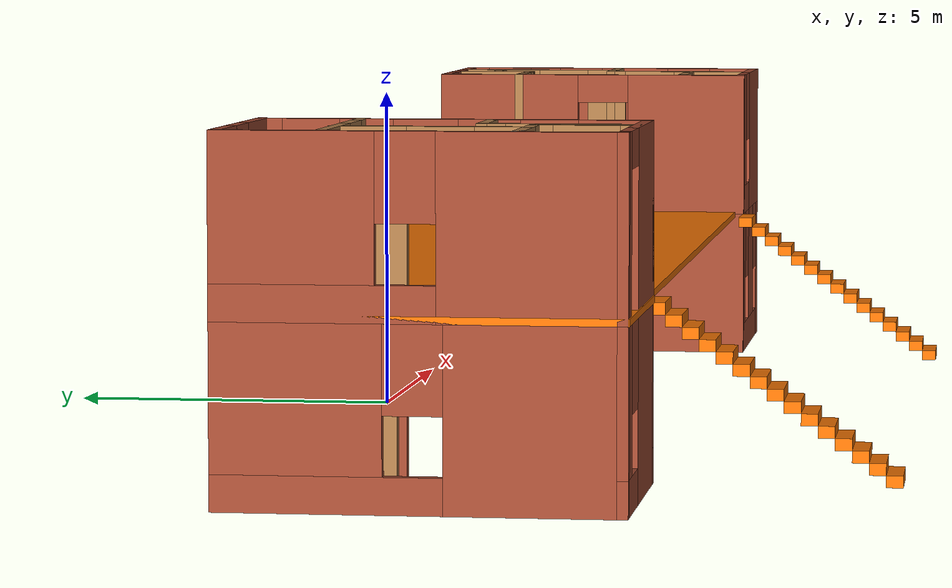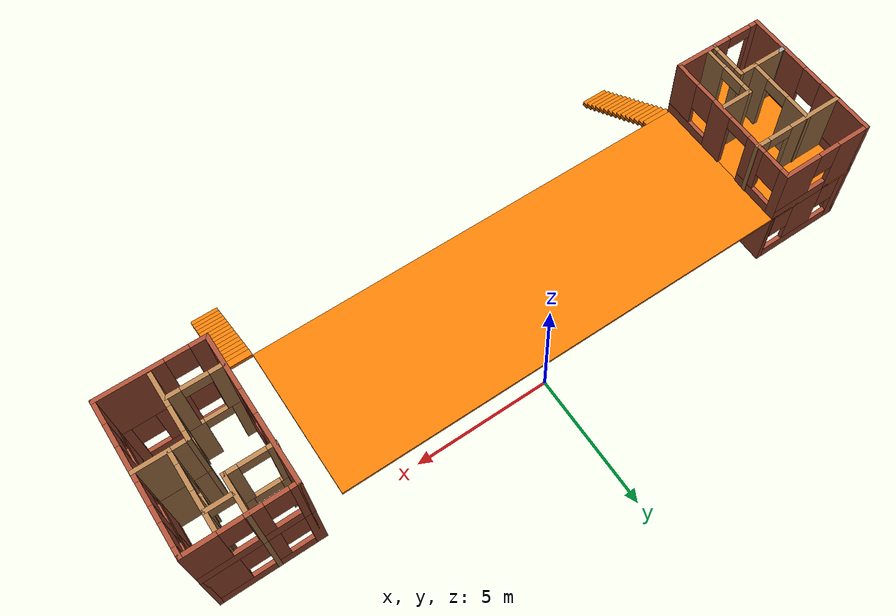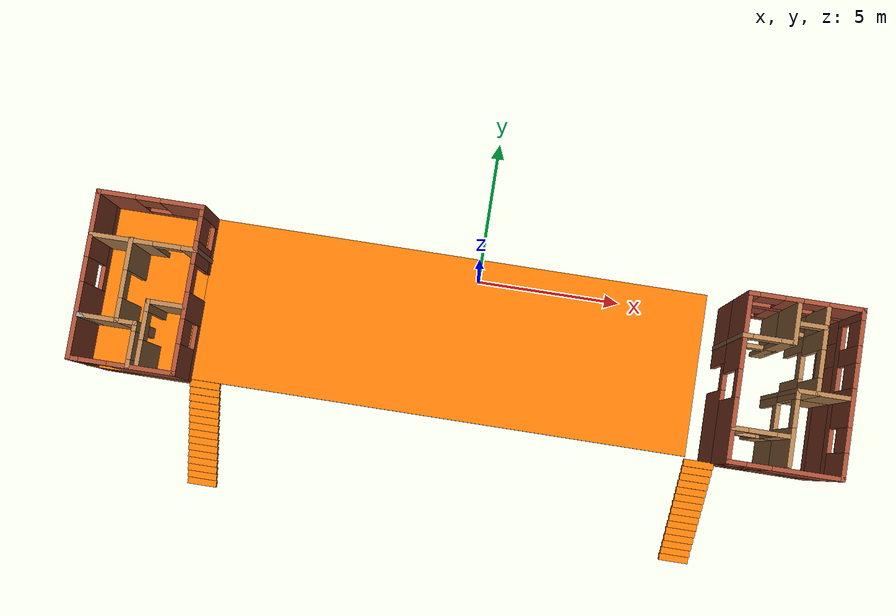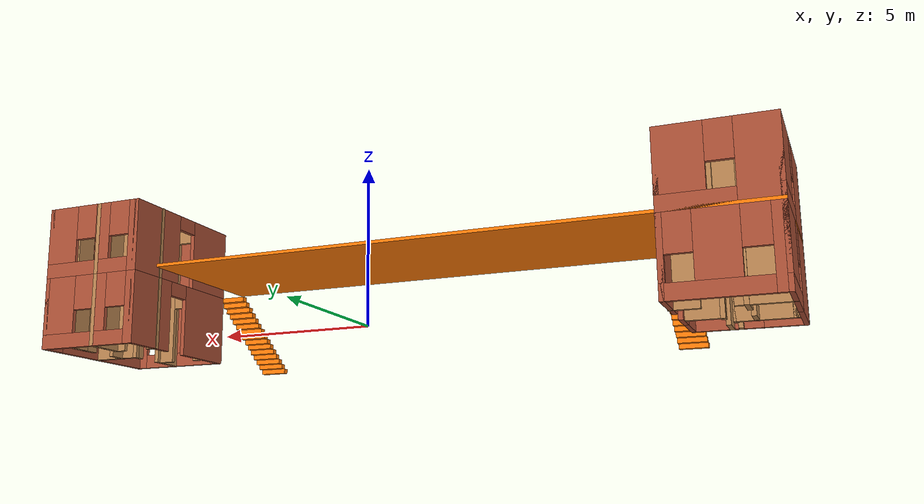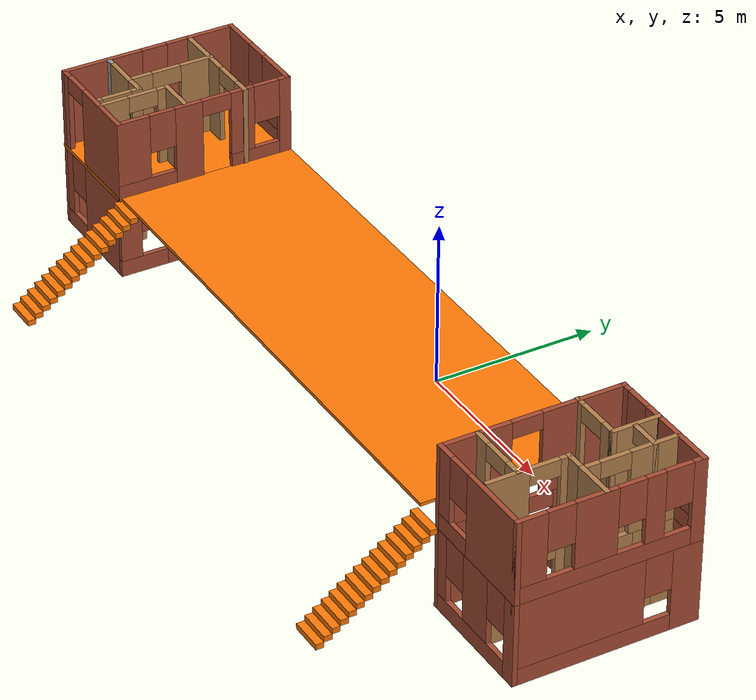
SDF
<?xml version='1.0'?>
<sdf version='1.6'>
  <model name='Building'>
    <pose frame=''>-0.047811 -4.11763 0 0 -0 0</pose>
    <link name='Floor_1'>
      <pose frame=''>-0 1.73959 2.5 0 -0 0</pose>
      <visual name='Floor_1_Visual_0'>
        <pose frame=''>-10.5996 0 0.05 0 -0 0</pose>
        <geometry>
          <box>
            <size>3.457 5.5163 0.1</size>
          </box>
        </geometry>
        <material>
          <script>
            <uri>file://media/materials/scripts/gazebo.material</uri>
            <name>Gazebo/Grey</name>
          </script>
          <ambient>0.996078 0.47451 0.0196078 1</ambient>
        </material>
        <meta>
          <layer>1</layer>
        </meta>
      </visual>
      <collision name='Floor_1_Collision_0'>
        <geometry>
          <box>
            <size>3.457 5.5163 0.1</size>
          </box>
        </geometry>
        <pose frame=''>-10.5996 0 0.05 0 -0 0</pose>
      </collision>
      <visual name='Floor_1_Visual_1'>
        <pose frame=''>-0.590304 0.045102 0.05 0 -0 0</pose>
        <geometry>
          <box>
            <size>16.5615 5.4261 0.1</size>
          </box>
        </geometry>
        <material>
          <script>
            <uri>file://media/materials/scripts/gazebo.material</uri>
            <name>Gazebo/Grey</name>
          </script>
          <ambient>0.996078 0.47451 0.0196078 1</ambient>
        </material>
        <meta>
          <layer>1</layer>
        </meta>
      </visual>
      <collision name='Floor_1_Collision_1'>
        <geometry>
          <box>
            <size>16.5615 5.4261 0.1</size>
          </box>
        </geometry>
        <pose frame=''>-0.590304 0.045102 0.05 0 -0 0</pose>
      </collision>
    </link>
    <link name='Stairs_1'>
      <visual name='Stairs_1_Visual_0'>
        <pose frame=''>-8.37106 -4.31169 0.083333 0 -0 -3.14159</pose>
        <geometry>
          <box>
            <size>1 0.233333 0.166667</size>
          </box>
        </geometry>
        <material>
          <script>
            <uri>file://media/materials/scripts/gazebo.material</uri>
            <name>Gazebo/Grey</name>
          </script>
          <ambient>0.996078 0.47451 0.0196078 1</ambient>
        </material>
        <meta>
          <layer>0</layer>
        </meta>
      </visual>
      <collision name='Stairs_1_Collision_0'>
        <geometry>
          <box>
            <size>1 0.233333 0.166667</size>
          </box>
        </geometry>
        <pose frame=''>-8.37106 -4.31169 0.083333 0 -0 -3.14159</pose>
      </collision>
      <visual name='Stairs_1_Visual_1'>
        <pose frame=''>-8.37106 -4.07835 0.25 0 -0 -3.14159</pose>
        <geometry>
          <box>
            <size>1 0.233333 0.166667</size>
          </box>
        </geometry>
        <material>
          <script>
            <uri>file://media/materials/scripts/gazebo.material</uri>
            <name>Gazebo/Grey</name>
          </script>
          <ambient>0.996078 0.47451 0.0196078 1</ambient>
        </material>
        <meta>
          <layer>0</layer>
        </meta>
      </visual>
      <collision name='Stairs_1_Collision_1'>
        <geometry>
          <box>
            <size>1 0.233333 0.166667</size>
          </box>
        </geometry>
        <pose frame=''>-8.37106 -4.07835 0.25 0 -0 -3.14159</pose>
      </collision>
      <visual name='Stairs_1_Visual_2'>
        <pose frame=''>-8.37106 -3.84502 0.416667 0 -0 -3.14159</pose>
        <geometry>
          <box>
            <size>1 0.233333 0.166667</size>
          </box>
        </geometry>
        <material>
          <script>
            <uri>file://media/materials/scripts/gazebo.material</uri>
            <name>Gazebo/Grey</name>
          </script>
          <ambient>0.996078 0.47451 0.0196078 1</ambient>
        </material>
        <meta>
          <layer>0</layer>
        </meta>
      </visual>
      <collision name='Stairs_1_Collision_2'>
        <geometry>
          <box>
            <size>1 0.233333 0.166667</size>
          </box>
        </geometry>
        <pose frame=''>-8.37106 -3.84502 0.416667 0 -0 -3.14159</pose>
      </collision>
      <visual name='Stairs_1_Visual_3'>
        <pose frame=''>-8.37106 -3.61169 0.583333 0 -0 -3.14159</pose>
        <geometry>
          <box>
            <size>1 0.233333 0.166667</size>
          </box>
        </geometry>
        <material>
          <script>
            <uri>file://media/materials/scripts/gazebo.material</uri>
            <name>Gazebo/Grey</name>
          </script>
          <ambient>0.996078 0.47451 0.0196078 1</ambient>
        </material>
        <meta>
          <layer>0</layer>
        </meta>
      </visual>
      <collision name='Stairs_1_Collision_3'>
        <geometry>
          <box>
            <size>1 0.233333 0.166667</size>
          </box>
        </geometry>
        <pose frame=''>-8.37106 -3.61169 0.583333 0 -0 -3.14159</pose>
      </collision>
      <visual name='Stairs_1_Visual_4'>
        <pose frame=''>-8.37106 -3.37835 0.75 0 -0 -3.14159</pose>
        <geometry>
          <box>
            <size>1 0.233333 0.166667</size>
          </box>
        </geometry>
        <material>
          <script>
            <uri>file://media/materials/scripts/gazebo.material</uri>
            <name>Gazebo/Grey</name>
          </script>
          <ambient>0.996078 0.47451 0.0196078 1</ambient>
        </material>
        <meta>
          <layer>0</layer>
        </meta>
      </visual>
      <collision name='Stairs_1_Collision_4'>
        <geometry>
          <box>
            <size>1 0.233333 0.166667</size>
          </box>
        </geometry>
        <pose frame=''>-8.37106 -3.37835 0.75 0 -0 -3.14159</pose>
      </collision>
      <visual name='Stairs_1_Visual_5'>
        <pose frame=''>-8.37106 -3.14502 0.916667 0 -0 -3.14159</pose>
        <geometry>
          <box>
            <size>1 0.233333 0.166667</size>
          </box>
        </geometry>
        <material>
          <script>
            <uri>file://media/materials/scripts/gazebo.material</uri>
            <name>Gazebo/Grey</name>
          </script>
          <ambient>0.996078 0.47451 0.0196078 1</ambient>
        </material>
        <meta>
          <layer>0</layer>
        </meta>
      </visual>
      <collision name='Stairs_1_Collision_5'>
        <geometry>
          <box>
            <size>1 0.233333 0.166667</size>
          </box>
        </geometry>
        <pose frame=''>-8.37106 -3.14502 0.916667 0 -0 -3.14159</pose>
      </collision>
      <visual name='Stairs_1_Visual_6'>
        <pose frame=''>-8.37106 -2.91169 1.08333 0 -0 -3.14159</pose>
        <geometry>
          <box>
            <size>1 0.233333 0.166667</size>
          </box>
        </geometry>
        <material>
          <script>
            <uri>file://media/materials/scripts/gazebo.material</uri>
            <name>Gazebo/Grey</name>
          </script>
          <ambient>0.996078 0.47451 0.0196078 1</ambient>
        </material>
        <meta>
          <layer>0</layer>
        </meta>
      </visual>
      <collision name='Stairs_1_Collision_6'>
        <geometry>
          <box>
            <size>1 0.233333 0.166667</size>
          </box>
        </geometry>
        <pose frame=''>-8.37106 -2.91169 1.08333 0 -0 -3.14159</pose>
      </collision>
      <visual name='Stairs_1_Visual_7'>
        <pose frame=''>-8.37106 -2.67835 1.25 0 -0 -3.14159</pose>
        <geometry>
          <box>
            <size>1 0.233333 0.166667</size>
          </box>
        </geometry>
        <material>
          <script>
            <uri>file://media/materials/scripts/gazebo.material</uri>
            <name>Gazebo/Grey</name>
          </script>
          <ambient>0.996078 0.47451 0.0196078 1</ambient>
        </material>
        <meta>
          <layer>0</layer>
        </meta>
      </visual>
      <collision name='Stairs_1_Collision_7'>
        <geometry>
          <box>
            <size>1 0.233333 0.166667</size>
          </box>
        </geometry>
        <pose frame=''>-8.37106 -2.67835 1.25 0 -0 -3.14159</pose>
      </collision>
      <visual name='Stairs_1_Visual_8'>
        <pose frame=''>-8.37106 -2.44502 1.41667 0 -0 -3.14159</pose>
        <geometry>
          <box>
            <size>1 0.233333 0.166667</size>
          </box>
        </geometry>
        <material>
          <script>
            <uri>file://media/materials/scripts/gazebo.material</uri>
            <name>Gazebo/Grey</name>
          </script>
          <ambient>0.996078 0.47451 0.0196078 1</ambient>
        </material>
        <meta>
          <layer>0</layer>
        </meta>
      </visual>
      <collision name='Stairs_1_Collision_8'>
        <geometry>
          <box>
            <size>1 0.233333 0.166667</size>
          </box>
        </geometry>
        <pose frame=''>-8.37106 -2.44502 1.41667 0 -0 -3.14159</pose>
      </collision>
      <visual name='Stairs_1_Visual_9'>
        <pose frame=''>-8.37106 -2.21169 1.58333 0 -0 -3.14159</pose>
        <geometry>
          <box>
            <size>1 0.233333 0.166667</size>
          </box>
        </geometry>
        <material>
          <script>
            <uri>file://media/materials/scripts/gazebo.material</uri>
            <name>Gazebo/Grey</name>
          </script>
          <ambient>0.996078 0.47451 0.0196078 1</ambient>
        </material>
        <meta>
          <layer>0</layer>
        </meta>
      </visual>
      <collision name='Stairs_1_Collision_9'>
        <geometry>
          <box>
            <size>1 0.233333 0.166667</size>
          </box>
        </geometry>
        <pose frame=''>-8.37106 -2.21169 1.58333 0 -0 -3.14159</pose>
      </collision>
      <visual name='Stairs_1_Visual_10'>
        <pose frame=''>-8.37106 -1.97835 1.75 0 -0 -3.14159</pose>
        <geometry>
          <box>
            <size>1 0.233333 0.166667</size>
          </box>
        </geometry>
        <material>
          <script>
            <uri>file://media/materials/scripts/gazebo.material</uri>
            <name>Gazebo/Grey</name>
          </script>
          <ambient>0.996078 0.47451 0.0196078 1</ambient>
        </material>
        <meta>
          <layer>0</layer>
        </meta>
      </visual>
      <collision name='Stairs_1_Collision_10'>
        <geometry>
          <box>
            <size>1 0.233333 0.166667</size>
          </box>
        </geometry>
        <pose frame=''>-8.37106 -1.97835 1.75 0 -0 -3.14159</pose>
      </collision>
      <visual name='Stairs_1_Visual_11'>
        <pose frame=''>-8.37106 -1.74502 1.91667 0 -0 -3.14159</pose>
        <geometry>
          <box>
            <size>1 0.233333 0.166667</size>
          </box>
        </geometry>
        <material>
          <script>
            <uri>file://media/materials/scripts/gazebo.material</uri>
            <name>Gazebo/Grey</name>
          </script>
          <ambient>0.996078 0.47451 0.0196078 1</ambient>
        </material>
        <meta>
          <layer>0</layer>
        </meta>
      </visual>
      <collision name='Stairs_1_Collision_11'>
        <geometry>
          <box>
            <size>1 0.233333 0.166667</size>
          </box>
        </geometry>
        <pose frame=''>-8.37106 -1.74502 1.91667 0 -0 -3.14159</pose>
      </collision>
      <visual name='Stairs_1_Visual_12'>
        <pose frame=''>-8.37106 -1.51169 2.08333 0 -0 -3.14159</pose>
        <geometry>
          <box>
            <size>1 0.233333 0.166667</size>
          </box>
        </geometry>
        <material>
          <script>
            <uri>file://media/materials/scripts/gazebo.material</uri>
            <name>Gazebo/Grey</name>
          </script>
          <ambient>0.996078 0.47451 0.0196078 1</ambient>
        </material>
        <meta>
          <layer>0</layer>
        </meta>
      </visual>
      <collision name='Stairs_1_Collision_12'>
        <geometry>
          <box>
            <size>1 0.233333 0.166667</size>
          </box>
        </geometry>
        <pose frame=''>-8.37106 -1.51169 2.08333 0 -0 -3.14159</pose>
      </collision>
      <visual name='Stairs_1_Visual_13'>
        <pose frame=''>-8.37106 -1.27835 2.25 0 -0 -3.14159</pose>
        <geometry>
          <box>
            <size>1 0.233333 0.166667</size>
          </box>
        </geometry>
        <material>
          <script>
            <uri>file://media/materials/scripts/gazebo.material</uri>
            <name>Gazebo/Grey</name>
          </script>
          <ambient>0.996078 0.47451 0.0196078 1</ambient>
        </material>
        <meta>
          <layer>0</layer>
        </meta>
      </visual>
      <collision name='Stairs_1_Collision_13'>
        <geometry>
          <box>
            <size>1 0.233333 0.166667</size>
          </box>
        </geometry>
        <pose frame=''>-8.37106 -1.27835 2.25 0 -0 -3.14159</pose>
      </collision>
      <visual name='Stairs_1_Visual_14'>
        <pose frame=''>-8.37106 -1.04502 2.41667 0 -0 -3.14159</pose>
        <geometry>
          <box>
            <size>1 0.233333 0.166667</size>
          </box>
        </geometry>
        <material>
          <script>
            <uri>file://media/materials/scripts/gazebo.material</uri>
            <name>Gazebo/Grey</name>
          </script>
          <ambient>0.996078 0.47451 0.0196078 1</ambient>
        </material>
        <meta>
          <layer>0</layer>
        </meta>
      </visual>
      <collision name='Stairs_1_Collision_14'>
        <geometry>
          <box>
            <size>1 0.233333 0.166667</size>
          </box>
        </geometry>
        <pose frame=''>-8.37106 -1.04502 2.41667 0 -0 -3.14159</pose>
      </collision>
    </link>
    <link name='Stairs_2'>
      <visual name='Stairs_2_Visual_0'>
        <pose frame=''>8.19045 -4.38108 0.083333 0 -0 -3.14159</pose>
        <geometry>
          <box>
            <size>1 0.233333 0.166667</size>
          </box>
        </geometry>
        <material>
          <script>
            <uri>file://media/materials/scripts/gazebo.material</uri>
            <name>Gazebo/Grey</name>
          </script>
          <ambient>0.996078 0.47451 0.0196078 1</ambient>
        </material>
        <meta>
          <layer>0</layer>
        </meta>
      </visual>
      <collision name='Stairs_2_Collision_0'>
        <geometry>
          <box>
            <size>1 0.233333 0.166667</size>
          </box>
        </geometry>
        <pose frame=''>8.19045 -4.38108 0.083333 0 -0 -3.14159</pose>
      </collision>
      <visual name='Stairs_2_Visual_1'>
        <pose frame=''>8.19045 -4.14774 0.25 0 -0 -3.14159</pose>
        <geometry>
          <box>
            <size>1 0.233333 0.166667</size>
          </box>
        </geometry>
        <material>
          <script>
            <uri>file://media/materials/scripts/gazebo.material</uri>
            <name>Gazebo/Grey</name>
          </script>
          <ambient>0.996078 0.47451 0.0196078 1</ambient>
        </material>
        <meta>
          <layer>0</layer>
        </meta>
      </visual>
      <collision name='Stairs_2_Collision_1'>
        <geometry>
          <box>
            <size>1 0.233333 0.166667</size>
          </box>
        </geometry>
        <pose frame=''>8.19045 -4.14774 0.25 0 -0 -3.14159</pose>
      </collision>
      <visual name='Stairs_2_Visual_2'>
        <pose frame=''>8.19045 -3.91441 0.416667 0 -0 -3.14159</pose>
        <geometry>
          <box>
            <size>1 0.233333 0.166667</size>
          </box>
        </geometry>
        <material>
          <script>
            <uri>file://media/materials/scripts/gazebo.material</uri>
            <name>Gazebo/Grey</name>
          </script>
          <ambient>0.996078 0.47451 0.0196078 1</ambient>
        </material>
        <meta>
          <layer>0</layer>
        </meta>
      </visual>
      <collision name='Stairs_2_Collision_2'>
        <geometry>
          <box>
            <size>1 0.233333 0.166667</size>
          </box>
        </geometry>
        <pose frame=''>8.19045 -3.91441 0.416667 0 -0 -3.14159</pose>
      </collision>
      <visual name='Stairs_2_Visual_3'>
        <pose frame=''>8.19045 -3.68108 0.583333 0 -0 -3.14159</pose>
        <geometry>
          <box>
            <size>1 0.233333 0.166667</size>
          </box>
        </geometry>
        <material>
          <script>
            <uri>file://media/materials/scripts/gazebo.material</uri>
            <name>Gazebo/Grey</name>
          </script>
          <ambient>0.996078 0.47451 0.0196078 1</ambient>
        </material>
        <meta>
          <layer>0</layer>
        </meta>
      </visual>
      <collision name='Stairs_2_Collision_3'>
        <geometry>
          <box>
            <size>1 0.233333 0.166667</size>
          </box>
        </geometry>
        <pose frame=''>8.19045 -3.68108 0.583333 0 -0 -3.14159</pose>
      </collision>
      <visual name='Stairs_2_Visual_4'>
        <pose frame=''>8.19045 -3.44774 0.75 0 -0 -3.14159</pose>
        <geometry>
          <box>
            <size>1 0.233333 0.166667</size>
          </box>
        </geometry>
        <material>
          <script>
            <uri>file://media/materials/scripts/gazebo.material</uri>
            <name>Gazebo/Grey</name>
          </script>
          <ambient>0.996078 0.47451 0.0196078 1</ambient>
        </material>
        <meta>
          <layer>0</layer>
        </meta>
      </visual>
      <collision name='Stairs_2_Collision_4'>
        <geometry>
          <box>
            <size>1 0.233333 0.166667</size>
          </box>
        </geometry>
        <pose frame=''>8.19045 -3.44774 0.75 0 -0 -3.14159</pose>
      </collision>
      <visual name='Stairs_2_Visual_5'>
        <pose frame=''>8.19045 -3.21441 0.916667 0 -0 -3.14159</pose>
        <geometry>
          <box>
            <size>1 0.233333 0.166667</size>
          </box>
        </geometry>
        <material>
          <script>
            <uri>file://media/materials/scripts/gazebo.material</uri>
            <name>Gazebo/Grey</name>
          </script>
          <ambient>0.996078 0.47451 0.0196078 1</ambient>
        </material>
        <meta>
          <layer>0</layer>
        </meta>
      </visual>
      <collision name='Stairs_2_Collision_5'>
        <geometry>
          <box>
            <size>1 0.233333 0.166667</size>
          </box>
        </geometry>
        <pose frame=''>8.19045 -3.21441 0.916667 0 -0 -3.14159</pose>
      </collision>
      <visual name='Stairs_2_Visual_6'>
        <pose frame=''>8.19045 -2.98108 1.08333 0 -0 -3.14159</pose>
        <geometry>
          <box>
            <size>1 0.233333 0.166667</size>
          </box>
        </geometry>
        <material>
          <script>
            <uri>file://media/materials/scripts/gazebo.material</uri>
            <name>Gazebo/Grey</name>
          </script>
          <ambient>0.996078 0.47451 0.0196078 1</ambient>
        </material>
        <meta>
          <layer>0</layer>
        </meta>
      </visual>
      <collision name='Stairs_2_Collision_6'>
        <geometry>
          <box>
            <size>1 0.233333 0.166667</size>
          </box>
        </geometry>
        <pose frame=''>8.19045 -2.98108 1.08333 0 -0 -3.14159</pose>
      </collision>
      <visual name='Stairs_2_Visual_7'>
        <pose frame=''>8.19045 -2.74774 1.25 0 -0 -3.14159</pose>
        <geometry>
          <box>
            <size>1 0.233333 0.166667</size>
          </box>
        </geometry>
        <material>
          <script>
            <uri>file://media/materials/scripts/gazebo.material</uri>
            <name>Gazebo/Grey</name>
          </script>
          <ambient>0.996078 0.47451 0.0196078 1</ambient>
        </material>
        <meta>
          <layer>0</layer>
        </meta>
      </visual>
      <collision name='Stairs_2_Collision_7'>
        <geometry>
          <box>
            <size>1 0.233333 0.166667</size>
          </box>
        </geometry>
        <pose frame=''>8.19045 -2.74774 1.25 0 -0 -3.14159</pose>
      </collision>
      <visual name='Stairs_2_Visual_8'>
        <pose frame=''>8.19045 -2.51441 1.41667 0 -0 -3.14159</pose>
        <geometry>
          <box>
            <size>1 0.233333 0.166667</size>
          </box>
        </geometry>
        <material>
          <script>
            <uri>file://media/materials/scripts/gazebo.material</uri>
            <name>Gazebo/Grey</name>
          </script>
          <ambient>0.996078 0.47451 0.0196078 1</ambient>
        </material>
        <meta>
          <layer>0</layer>
        </meta>
      </visual>
      <collision name='Stairs_2_Collision_8'>
        <geometry>
          <box>
            <size>1 0.233333 0.166667</size>
          </box>
        </geometry>
        <pose frame=''>8.19045 -2.51441 1.41667 0 -0 -3.14159</pose>
      </collision>
      <visual name='Stairs_2_Visual_9'>
        <pose frame=''>8.19045 -2.28108 1.58333 0 -0 -3.14159</pose>
        <geometry>
          <box>
            <size>1 0.233333 0.166667</size>
          </box>
        </geometry>
        <material>
          <script>
            <uri>file://media/materials/scripts/gazebo.material</uri>
            <name>Gazebo/Grey</name>
          </script>
          <ambient>0.996078 0.47451 0.0196078 1</ambient>
        </material>
        <meta>
          <layer>0</layer>
        </meta>
      </visual>
      <collision name='Stairs_2_Collision_9'>
        <geometry>
          <box>
            <size>1 0.233333 0.166667</size>
          </box>
        </geometry>
        <pose frame=''>8.19045 -2.28108 1.58333 0 -0 -3.14159</pose>
      </collision>
      <visual name='Stairs_2_Visual_10'>
        <pose frame=''>8.19045 -2.04774 1.75 0 -0 -3.14159</pose>
        <geometry>
          <box>
            <size>1 0.233333 0.166667</size>
          </box>
        </geometry>
        <material>
          <script>
            <uri>file://media/materials/scripts/gazebo.material</uri>
            <name>Gazebo/Grey</name>
          </script>
          <ambient>0.996078 0.47451 0.0196078 1</ambient>
        </material>
        <meta>
          <layer>0</layer>
        </meta>
      </visual>
      <collision name='Stairs_2_Collision_10'>
        <geometry>
          <box>
            <size>1 0.233333 0.166667</size>
          </box>
        </geometry>
        <pose frame=''>8.19045 -2.04774 1.75 0 -0 -3.14159</pose>
      </collision>
      <visual name='Stairs_2_Visual_11'>
        <pose frame=''>8.19045 -1.81441 1.91667 0 -0 -3.14159</pose>
        <geometry>
          <box>
            <size>1 0.233333 0.166667</size>
          </box>
        </geometry>
        <material>
          <script>
            <uri>file://media/materials/scripts/gazebo.material</uri>
            <name>Gazebo/Grey</name>
          </script>
          <ambient>0.996078 0.47451 0.0196078 1</ambient>
        </material>
        <meta>
          <layer>0</layer>
        </meta>
      </visual>
      <collision name='Stairs_2_Collision_11'>
        <geometry>
          <box>
            <size>1 0.233333 0.166667</size>
          </box>
        </geometry>
        <pose frame=''>8.19045 -1.81441 1.91667 0 -0 -3.14159</pose>
      </collision>
      <visual name='Stairs_2_Visual_12'>
        <pose frame=''>8.19045 -1.58108 2.08333 0 -0 -3.14159</pose>
        <geometry>
          <box>
            <size>1 0.233333 0.166667</size>
          </box>
        </geometry>
        <material>
          <script>
            <uri>file://media/materials/scripts/gazebo.material</uri>
            <name>Gazebo/Grey</name>
          </script>
          <ambient>0.996078 0.47451 0.0196078 1</ambient>
        </material>
        <meta>
          <layer>0</layer>
        </meta>
      </visual>
      <collision name='Stairs_2_Collision_12'>
        <geometry>
          <box>
            <size>1 0.233333 0.166667</size>
          </box>
        </geometry>
        <pose frame=''>8.19045 -1.58108 2.08333 0 -0 -3.14159</pose>
      </collision>
      <visual name='Stairs_2_Visual_13'>
        <pose frame=''>8.19045 -1.34774 2.25 0 -0 -3.14159</pose>
        <geometry>
          <box>
            <size>1 0.233333 0.166667</size>
          </box>
        </geometry>
        <material>
          <script>
            <uri>file://media/materials/scripts/gazebo.material</uri>
            <name>Gazebo/Grey</name>
          </script>
          <ambient>0.996078 0.47451 0.0196078 1</ambient>
        </material>
        <meta>
          <layer>0</layer>
        </meta>
      </visual>
      <collision name='Stairs_2_Collision_13'>
        <geometry>
          <box>
            <size>1 0.233333 0.166667</size>
          </box>
        </geometry>
        <pose frame=''>8.19045 -1.34774 2.25 0 -0 -3.14159</pose>
      </collision>
      <visual name='Stairs_2_Visual_14'>
        <pose frame=''>8.19045 -1.11441 2.41667 0 -0 -3.14159</pose>
        <geometry>
          <box>
            <size>1 0.233333 0.166667</size>
          </box>
        </geometry>
        <material>
          <script>
            <uri>file://media/materials/scripts/gazebo.material</uri>
            <name>Gazebo/Grey</name>
          </script>
          <ambient>0.996078 0.47451 0.0196078 1</ambient>
        </material>
        <meta>
          <layer>0</layer>
        </meta>
      </visual>
      <collision name='Stairs_2_Collision_14'>
        <geometry>
          <box>
            <size>1 0.233333 0.166667</size>
          </box>
        </geometry>
        <pose frame=''>8.19045 -1.11441 2.41667 0 -0 -3.14159</pose>
      </collision>
    </link>
    <link name='Wall_12'>
      <pose frame=''>-10.5549 3.03491 0 0 -0 3.14159</pose>
      <visual name='Wall_12_Visual_0'>
        <pose frame=''>-1.28984 0 1.25 0 -0 0</pose>
        <geometry>
          <box>
            <size>0.920315 0.15 2.5</size>
          </box>
        </geometry>
        <material>
          <script>
            <uri>file://media/materials/scripts/gazebo.material</uri>
            <name>Gazebo/Wood</name>
          </script>
          <ambient>1 1 1 1</ambient>
        </material>
        <meta>
          <layer>0</layer>
        </meta>
      </visual>
      <collision name='Wall_12_Collision_0'>
        <geometry>
          <box>
            <size>0.920315 0.15 2.5</size>
          </box>
        </geometry>
        <pose frame=''>-1.28984 0 1.25 0 -0 0</pose>
      </collision>
      <visual name='Wall_12_Visual_1'>
        <pose frame=''>0.910157 0 1.25 0 -0 0</pose>
        <geometry>
          <box>
            <size>1.67969 0.15 2.5</size>
          </box>
        </geometry>
        <material>
          <script>
            <uri>file://media/materials/scripts/gazebo.material</uri>
            <name>Gazebo/Wood</name>
          </script>
          <ambient>1 1 1 1</ambient>
        </material>
        <meta>
          <layer>0</layer>
        </meta>
      </visual>
      <collision name='Wall_12_Collision_1'>
        <geometry>
          <box>
            <size>1.67969 0.15 2.5</size>
          </box>
        </geometry>
        <pose frame=''>0.910157 0 1.25 0 -0 0</pose>
      </collision>
      <visual name='Wall_12_Visual_2'>
        <pose frame=''>-0.379685 0 2.25 0 -0 0</pose>
        <geometry>
          <box>
            <size>0.9 0.15 0.5</size>
          </box>
        </geometry>
        <material>
          <script>
            <uri>file://media/materials/scripts/gazebo.material</uri>
            <name>Gazebo/Wood</name>
          </script>
          <ambient>1 1 1 1</ambient>
        </material>
        <meta>
          <layer>0</layer>
        </meta>
      </visual>
      <collision name='Wall_12_Collision_2'>
        <geometry>
          <box>
            <size>0.9 0.15 0.5</size>
          </box>
        </geometry>
        <pose frame=''>-0.379685 0 2.25 0 -0 0</pose>
      </collision>
    </link>
    <link name='Wall_14'>
      <pose frame=''>-10.9617 1.75804 0 0 -0 -1.5708</pose>
      <visual name='Wall_14_Visual_0'>
        <pose frame=''>-0.914843 0 1.25 0 -0 0</pose>
        <geometry>
          <box>
            <size>0.920314 0.15 2.5</size>
          </box>
        </geometry>
        <material>
          <script>
            <uri>file://media/materials/scripts/gazebo.material</uri>
            <name>Gazebo/Wood</name>
          </script>
          <ambient>1 1 1 1</ambient>
        </material>
        <meta>
          <layer>0</layer>
        </meta>
      </visual>
      <collision name='Wall_14_Collision_0'>
        <geometry>
          <box>
            <size>0.920314 0.15 2.5</size>
          </box>
        </geometry>
        <pose frame=''>-0.914843 0 1.25 0 -0 0</pose>
      </collision>
      <visual name='Wall_14_Visual_1'>
        <pose frame=''>0.910157 0 1.25 0 -0 0</pose>
        <geometry>
          <box>
            <size>0.929686 0.15 2.5</size>
          </box>
        </geometry>
        <material>
          <script>
            <uri>file://media/materials/scripts/gazebo.material</uri>
            <name>Gazebo/Wood</name>
          </script>
          <ambient>1 1 1 1</ambient>
        </material>
        <meta>
          <layer>0</layer>
        </meta>
      </visual>
      <collision name='Wall_14_Collision_1'>
        <geometry>
          <box>
            <size>0.929686 0.15 2.5</size>
          </box>
        </geometry>
        <pose frame=''>0.910157 0 1.25 0 -0 0</pose>
      </collision>
      <visual name='Wall_14_Visual_2'>
        <pose frame=''>-0.004686 0 2.25 0 -0 0</pose>
        <geometry>
          <box>
            <size>0.9 0.15 0.5</size>
          </box>
        </geometry>
        <material>
          <script>
            <uri>file://media/materials/scripts/gazebo.material</uri>
            <name>Gazebo/Wood</name>
          </script>
          <ambient>1 1 1 1</ambient>
        </material>
        <meta>
          <layer>0</layer>
        </meta>
      </visual>
      <collision name='Wall_14_Collision_2'>
        <geometry>
          <box>
            <size>0.9 0.15 0.5</size>
          </box>
        </geometry>
        <pose frame=''>-0.004686 0 2.25 0 -0 0</pose>
      </collision>
    </link>
    <link name='Wall_15'>
      <collision name='Wall_15_Collision'>
        <geometry>
          <box>
            <size>1.25 0.15 2.5</size>
          </box>
        </geometry>
        <pose frame=''>0 0 1.25 0 -0 0</pose>
      </collision>
      <visual name='Wall_15_Visual'>
        <pose frame=''>0 0 1.25 0 -0 0</pose>
        <geometry>
          <box>
            <size>1.25 0.15 2.5</size>
          </box>
        </geometry>
        <material>
          <script>
            <uri>file://media/materials/scripts/gazebo.material</uri>
            <name>Gazebo/Wood</name>
          </script>
          <ambient>1 1 1 1</ambient>
        </material>
        <meta>
          <layer>0</layer>
        </meta>
      </visual>
      <pose frame=''>-11.5117 0.458038 0 0 -0 3.14159</pose>
    </link>
    <link name='Wall_16'>
      <collision name='Wall_16_Collision'>
        <geometry>
          <box>
            <size>0.25 0.15 2.5</size>
          </box>
        </geometry>
        <pose frame=''>0 0 1.25 0 -0 0</pose>
      </collision>
      <visual name='Wall_16_Visual'>
        <pose frame=''>0 0 1.25 0 -0 0</pose>
        <geometry>
          <box>
            <size>0.25 0.15 2.5</size>
          </box>
        </geometry>
        <material>
          <script>
            <uri>file://media/materials/scripts/gazebo.material</uri>
            <name>Gazebo/Wood</name>
          </script>
          <ambient>1 1 1 1</ambient>
        </material>
        <meta>
          <layer>0</layer>
        </meta>
      </visual>
      <pose frame=''>-12.1117 0.458038 0 0 -0 3.14159</pose>
    </link>
    <link name='Wall_18'>
      <collision name='Wall_18_Collision'>
        <geometry>
          <box>
            <size>0.75 0.15 2.5</size>
          </box>
        </geometry>
        <pose frame=''>0 0 1.25 0 -0 0</pose>
      </collision>
      <visual name='Wall_18_Visual'>
        <pose frame=''>0 0 1.25 0 -0 0</pose>
        <geometry>
          <box>
            <size>0.75 0.15 2.5</size>
          </box>
        </geometry>
        <material>
          <script>
            <uri>file://media/materials/scripts/gazebo.material</uri>
            <name>Gazebo/Wood</name>
          </script>
          <ambient>1 1 1 1</ambient>
        </material>
        <meta>
          <layer>0</layer>
        </meta>
      </visual>
      <pose frame=''>-10.6617 0.458038 0 0 -0 0</pose>
    </link>
    <link name='Wall_19'>
      <pose frame=''>-10.3617 -0.216962 0 0 -0 -1.5708</pose>
      <visual name='Wall_19_Visual_0'>
        <pose frame=''>-0.606792 0 1.25 0 -0 0</pose>
        <geometry>
          <box>
            <size>0.286415 0.15 2.5</size>
          </box>
        </geometry>
        <material>
          <script>
            <uri>file://media/materials/scripts/gazebo.material</uri>
            <name>Gazebo/Wood</name>
          </script>
          <ambient>1 1 1 1</ambient>
        </material>
        <meta>
          <layer>0</layer>
        </meta>
      </visual>
      <collision name='Wall_19_Collision_0'>
        <geometry>
          <box>
            <size>0.286415 0.15 2.5</size>
          </box>
        </geometry>
        <pose frame=''>-0.606792 0 1.25 0 -0 0</pose>
      </collision>
      <visual name='Wall_19_Visual_1'>
        <pose frame=''>0.593208 0 1.25 0 -0 0</pose>
        <geometry>
          <box>
            <size>0.313585 0.15 2.5</size>
          </box>
        </geometry>
        <material>
          <script>
            <uri>file://media/materials/scripts/gazebo.material</uri>
            <name>Gazebo/Wood</name>
          </script>
          <ambient>1 1 1 1</ambient>
        </material>
        <meta>
          <layer>0</layer>
        </meta>
      </visual>
      <collision name='Wall_19_Collision_1'>
        <geometry>
          <box>
            <size>0.313585 0.15 2.5</size>
          </box>
        </geometry>
        <pose frame=''>0.593208 0 1.25 0 -0 0</pose>
      </collision>
      <visual name='Wall_19_Visual_2'>
        <pose frame=''>-0.013585 0 2.25 0 -0 0</pose>
        <geometry>
          <box>
            <size>0.9 0.15 0.5</size>
          </box>
        </geometry>
        <material>
          <script>
            <uri>file://media/materials/scripts/gazebo.material</uri>
            <name>Gazebo/Wood</name>
          </script>
          <ambient>1 1 1 1</ambient>
        </material>
        <meta>
          <layer>0</layer>
        </meta>
      </visual>
      <collision name='Wall_19_Collision_2'>
        <geometry>
          <box>
            <size>0.9 0.15 0.5</size>
          </box>
        </geometry>
        <pose frame=''>-0.013585 0 2.25 0 -0 0</pose>
      </collision>
    </link>
    <link name='Wall_21'>
      <pose frame=''>-10.0827 0.152704 0 0 -0 1.5708</pose>
      <visual name='Wall_21_Visual_0'>
        <pose frame=''>-0.618582 0 1.25 0 -0 0</pose>
        <geometry>
          <box>
            <size>1.01284 0.15 2.5</size>
          </box>
        </geometry>
        <material>
          <script>
            <uri>file://media/materials/scripts/gazebo.material</uri>
            <name>Gazebo/Wood</name>
          </script>
          <ambient>1 1 1 1</ambient>
        </material>
        <meta>
          <layer>0</layer>
        </meta>
      </visual>
      <collision name='Wall_21_Collision_0'>
        <geometry>
          <box>
            <size>1.01284 0.15 2.5</size>
          </box>
        </geometry>
        <pose frame=''>-0.618582 0 1.25 0 -0 0</pose>
      </collision>
      <visual name='Wall_21_Visual_1'>
        <pose frame=''>0.956418 0 1.25 0 -0 0</pose>
        <geometry>
          <box>
            <size>0.337163 0.15 2.5</size>
          </box>
        </geometry>
        <material>
          <script>
            <uri>file://media/materials/scripts/gazebo.material</uri>
            <name>Gazebo/Wood</name>
          </script>
          <ambient>1 1 1 1</ambient>
        </material>
        <meta>
          <layer>0</layer>
        </meta>
      </visual>
      <collision name='Wall_21_Collision_1'>
        <geometry>
          <box>
            <size>0.337163 0.15 2.5</size>
          </box>
        </geometry>
        <pose frame=''>0.956418 0 1.25 0 -0 0</pose>
      </collision>
      <visual name='Wall_21_Visual_2'>
        <pose frame=''>0.337837 0 2.25 0 -0 0</pose>
        <geometry>
          <box>
            <size>0.9 0.15 0.5</size>
          </box>
        </geometry>
        <material>
          <script>
            <uri>file://media/materials/scripts/gazebo.material</uri>
            <name>Gazebo/Wood</name>
          </script>
          <ambient>1 1 1 1</ambient>
        </material>
        <meta>
          <layer>0</layer>
        </meta>
      </visual>
      <collision name='Wall_21_Collision_2'>
        <geometry>
          <box>
            <size>0.9 0.15 0.5</size>
          </box>
        </geometry>
        <pose frame=''>0.337837 0 2.25 0 -0 0</pose>
      </collision>
    </link>
    <link name='Wall_22'>
      <collision name='Wall_22_Collision'>
        <geometry>
          <box>
            <size>1.25 0.15 2.5</size>
          </box>
        </geometry>
        <pose frame=''>0 0 1.25 0 -0 0</pose>
      </collision>
      <visual name='Wall_22_Visual'>
        <pose frame=''>0 0 1.25 0 -0 0</pose>
        <geometry>
          <box>
            <size>1.25 0.15 2.5</size>
          </box>
        </geometry>
        <material>
          <script>
            <uri>file://media/materials/scripts/gazebo.material</uri>
            <name>Gazebo/Wood</name>
          </script>
          <ambient>1 1 1 1</ambient>
        </material>
        <meta>
          <layer>0</layer>
        </meta>
      </visual>
      <pose frame=''>-9.53273 1.2027 0 0 -0 0</pose>
    </link>
    <link name='Wall_25'>
      <pose frame=''>8.65306 1.73144 0 0 -0 1.5708</pose>
      <visual name='Wall_25_Visual_0'>
        <pose frame=''>-1.51497 0 1.25 0 -0 0</pose>
        <geometry>
          <box>
            <size>2.47006 0.15 2.5</size>
          </box>
        </geometry>
        <material>
          <script>
            <uri>file://media/materials/scripts/gazebo.material</uri>
            <name>Gazebo/Bricks</name>
          </script>
          <ambient>1 1 1 1</ambient>
        </material>
        <meta>
          <layer>0</layer>
        </meta>
      </visual>
      <collision name='Wall_25_Collision_0'>
        <geometry>
          <box>
            <size>2.47006 0.15 2.5</size>
          </box>
        </geometry>
        <pose frame=''>-1.51497 0 1.25 0 -0 0</pose>
      </collision>
      <visual name='Wall_25_Visual_1'>
        <pose frame=''>1.68503 0 1.25 0 -0 0</pose>
        <geometry>
          <box>
            <size>2.12994 0.15 2.5</size>
          </box>
        </geometry>
        <material>
          <script>
            <uri>file://media/materials/scripts/gazebo.material</uri>
            <name>Gazebo/Bricks</name>
          </script>
          <ambient>1 1 1 1</ambient>
        </material>
        <meta>
          <layer>0</layer>
        </meta>
      </visual>
      <collision name='Wall_25_Collision_1'>
        <geometry>
          <box>
            <size>2.12994 0.15 2.5</size>
          </box>
        </geometry>
        <pose frame=''>1.68503 0 1.25 0 -0 0</pose>
      </collision>
      <visual name='Wall_25_Visual_2'>
        <pose frame=''>0.170065 0 2.25 0 -0 0</pose>
        <geometry>
          <box>
            <size>0.9 0.15 0.5</size>
          </box>
        </geometry>
        <material>
          <script>
            <uri>file://media/materials/scripts/gazebo.material</uri>
            <name>Gazebo/Bricks</name>
          </script>
          <ambient>1 1 1 1</ambient>
        </material>
        <meta>
          <layer>0</layer>
        </meta>
      </visual>
      <collision name='Wall_25_Collision_2'>
        <geometry>
          <box>
            <size>0.9 0.15 0.5</size>
          </box>
        </geometry>
        <pose frame=''>0.170065 0 2.25 0 -0 0</pose>
      </collision>
    </link>
    <link name='Wall_26'>
      <pose frame=''>10.4531 4.40644 0 0 -0 0</pose>
      <visual name='Wall_26_Visual_0'>
        <pose frame=''>-1.69054 0 1.25 0 -0 0</pose>
        <geometry>
          <box>
            <size>0.368918 0.15 2.5</size>
          </box>
        </geometry>
        <material>
          <script>
            <uri>file://media/materials/scripts/gazebo.material</uri>
            <name>Gazebo/Bricks</name>
          </script>
          <ambient>1 1 1 1</ambient>
        </material>
        <meta>
          <layer>0</layer>
        </meta>
      </visual>
      <collision name='Wall_26_Collision_0'>
        <geometry>
          <box>
            <size>0.368918 0.15 2.5</size>
          </box>
        </geometry>
        <pose frame=''>-1.69054 0 1.25 0 -0 0</pose>
      </collision>
      <visual name='Wall_26_Visual_1'>
        <pose frame=''>0.184459 0 0.25 0 -0 0</pose>
        <geometry>
          <box>
            <size>3.38108 0.15 0.5</size>
          </box>
        </geometry>
        <material>
          <script>
            <uri>file://media/materials/scripts/gazebo.material</uri>
            <name>Gazebo/Bricks</name>
          </script>
          <ambient>1 1 1 1</ambient>
        </material>
        <meta>
          <layer>0</layer>
        </meta>
      </visual>
      <collision name='Wall_26_Collision_1'>
        <geometry>
          <box>
            <size>3.38108 0.15 0.5</size>
          </box>
        </geometry>
        <pose frame=''>0.184459 0 0.25 0 -0 0</pose>
      </collision>
      <visual name='Wall_26_Visual_2'>
        <pose frame=''>-0.44686 0 1.5 0 -0 0</pose>
        <geometry>
          <box>
            <size>0.518444 0.15 2</size>
          </box>
        </geometry>
        <material>
          <script>
            <uri>file://media/materials/scripts/gazebo.material</uri>
            <name>Gazebo/Bricks</name>
          </script>
          <ambient>1 1 1 1</ambient>
        </material>
        <meta>
          <layer>0</layer>
        </meta>
      </visual>
      <collision name='Wall_26_Collision_2'>
        <geometry>
          <box>
            <size>0.518444 0.15 2</size>
          </box>
        </geometry>
        <pose frame=''>-0.44686 0 1.5 0 -0 0</pose>
      </collision>
      <visual name='Wall_26_Visual_3'>
        <pose frame=''>1.24368 0 1.5 0 -0 0</pose>
        <geometry>
          <box>
            <size>1.26264 0.15 2</size>
          </box>
        </geometry>
        <material>
          <script>
            <uri>file://media/materials/scripts/gazebo.material</uri>
            <name>Gazebo/Bricks</name>
          </script>
          <ambient>1 1 1 1</ambient>
        </material>
        <meta>
          <layer>0</layer>
        </meta>
      </visual>
      <collision name='Wall_26_Collision_3'>
        <geometry>
          <box>
            <size>1.26264 0.15 2</size>
          </box>
        </geometry>
        <pose frame=''>1.24368 0 1.5 0 -0 0</pose>
      </collision>
      <visual name='Wall_26_Visual_4'>
        <pose frame=''>-1.10608 0 1.9 0 -0 0</pose>
        <geometry>
          <box>
            <size>0.8 0.15 1.2</size>
          </box>
        </geometry>
        <material>
          <script>
            <uri>file://media/materials/scripts/gazebo.material</uri>
            <name>Gazebo/Bricks</name>
          </script>
          <ambient>1 1 1 1</ambient>
        </material>
        <meta>
          <layer>0</layer>
        </meta>
      </visual>
      <collision name='Wall_26_Collision_4'>
        <geometry>
          <box>
            <size>0.8 0.15 1.2</size>
          </box>
        </geometry>
        <pose frame=''>-1.10608 0 1.9 0 -0 0</pose>
      </collision>
      <visual name='Wall_26_Visual_5'>
        <pose frame=''>0.212362 0 1.9 0 -0 0</pose>
        <geometry>
          <box>
            <size>0.8 0.15 1.2</size>
          </box>
        </geometry>
        <material>
          <script>
            <uri>file://media/materials/scripts/gazebo.material</uri>
            <name>Gazebo/Bricks</name>
          </script>
          <ambient>1 1 1 1</ambient>
        </material>
        <meta>
          <layer>0</layer>
        </meta>
      </visual>
      <collision name='Wall_26_Collision_5'>
        <geometry>
          <box>
            <size>0.8 0.15 1.2</size>
          </box>
        </geometry>
        <pose frame=''>0.212362 0 1.9 0 -0 0</pose>
      </collision>
    </link>
    <link name='Wall_27'>
      <pose frame=''>12.2531 1.73144 0 0 -0 -1.5708</pose>
      <visual name='Wall_27_Visual_0'>
        <pose frame=''>-2.30769 0 1.25 0 -0 0</pose>
        <geometry>
          <box>
            <size>0.884621 0.15 2.5</size>
          </box>
        </geometry>
        <material>
          <script>
            <uri>file://media/materials/scripts/gazebo.material</uri>
            <name>Gazebo/Bricks</name>
          </script>
          <ambient>1 1 1 1</ambient>
        </material>
        <meta>
          <layer>0</layer>
        </meta>
      </visual>
      <collision name='Wall_27_Collision_0'>
        <geometry>
          <box>
            <size>0.884621 0.15 2.5</size>
          </box>
        </geometry>
        <pose frame=''>-2.30769 0 1.25 0 -0 0</pose>
      </collision>
      <visual name='Wall_27_Visual_1'>
        <pose frame=''>0.442311 0 0.25 0 -0 0</pose>
        <geometry>
          <box>
            <size>4.61538 0.15 0.5</size>
          </box>
        </geometry>
        <material>
          <script>
            <uri>file://media/materials/scripts/gazebo.material</uri>
            <name>Gazebo/Bricks</name>
          </script>
          <ambient>1 1 1 1</ambient>
        </material>
        <meta>
          <layer>0</layer>
        </meta>
      </visual>
      <collision name='Wall_27_Collision_1'>
        <geometry>
          <box>
            <size>4.61538 0.15 0.5</size>
          </box>
        </geometry>
        <pose frame=''>0.442311 0 0.25 0 -0 0</pose>
      </collision>
      <visual name='Wall_27_Visual_2'>
        <pose frame=''>0.842311 0 1.5 0 -0 0</pose>
        <geometry>
          <box>
            <size>3.81538 0.15 2</size>
          </box>
        </geometry>
        <material>
          <script>
            <uri>file://media/materials/scripts/gazebo.material</uri>
            <name>Gazebo/Bricks</name>
          </script>
          <ambient>1 1 1 1</ambient>
        </material>
        <meta>
          <layer>0</layer>
        </meta>
      </visual>
      <collision name='Wall_27_Collision_2'>
        <geometry>
          <box>
            <size>3.81538 0.15 2</size>
          </box>
        </geometry>
        <pose frame=''>0.842311 0 1.5 0 -0 0</pose>
      </collision>
      <visual name='Wall_27_Visual_3'>
        <pose frame=''>-1.46538 0 1.9 0 -0 0</pose>
        <geometry>
          <box>
            <size>0.8 0.15 1.2</size>
          </box>
        </geometry>
        <material>
          <script>
            <uri>file://media/materials/scripts/gazebo.material</uri>
            <name>Gazebo/Bricks</name>
          </script>
          <ambient>1 1 1 1</ambient>
        </material>
        <meta>
          <layer>0</layer>
        </meta>
      </visual>
      <collision name='Wall_27_Collision_3'>
        <geometry>
          <box>
            <size>0.8 0.15 1.2</size>
          </box>
        </geometry>
        <pose frame=''>-1.46538 0 1.9 0 -0 0</pose>
      </collision>
    </link>
    <link name='Wall_28'>
      <pose frame=''>10.4531 -0.943557 0 0 -0 3.14159</pose>
      <visual name='Wall_28_Visual_0'>
        <pose frame=''>-1.64847 0 1.25 0 -0 0</pose>
        <geometry>
          <box>
            <size>0.453066 0.15 2.5</size>
          </box>
        </geometry>
        <material>
          <script>
            <uri>file://media/materials/scripts/gazebo.material</uri>
            <name>Gazebo/Bricks</name>
          </script>
          <ambient>1 1 1 1</ambient>
        </material>
        <meta>
          <layer>0</layer>
        </meta>
      </visual>
      <collision name='Wall_28_Collision_0'>
        <geometry>
          <box>
            <size>0.453066 0.15 2.5</size>
          </box>
        </geometry>
        <pose frame=''>-1.64847 0 1.25 0 -0 0</pose>
      </collision>
      <visual name='Wall_28_Visual_1'>
        <pose frame=''>0.226533 0 0.25 0 -0 0</pose>
        <geometry>
          <box>
            <size>3.29693 0.15 0.5</size>
          </box>
        </geometry>
        <material>
          <script>
            <uri>file://media/materials/scripts/gazebo.material</uri>
            <name>Gazebo/Bricks</name>
          </script>
          <ambient>1 1 1 1</ambient>
        </material>
        <meta>
          <layer>0</layer>
        </meta>
      </visual>
      <collision name='Wall_28_Collision_1'>
        <geometry>
          <box>
            <size>3.29693 0.15 0.5</size>
          </box>
        </geometry>
        <pose frame=''>0.226533 0 0.25 0 -0 0</pose>
      </collision>
      <visual name='Wall_28_Visual_2'>
        <pose frame=''>-0.050448 0 1.5 0 -0 0</pose>
        <geometry>
          <box>
            <size>1.14297 0.15 2</size>
          </box>
        </geometry>
        <material>
          <script>
            <uri>file://media/materials/scripts/gazebo.material</uri>
            <name>Gazebo/Bricks</name>
          </script>
          <ambient>1 1 1 1</ambient>
        </material>
        <meta>
          <layer>0</layer>
        </meta>
      </visual>
      <collision name='Wall_28_Collision_2'>
        <geometry>
          <box>
            <size>1.14297 0.15 2</size>
          </box>
        </geometry>
        <pose frame=''>-0.050448 0 1.5 0 -0 0</pose>
      </collision>
      <visual name='Wall_28_Visual_3'>
        <pose frame=''>1.59802 0 1.5 0 -0 0</pose>
        <geometry>
          <box>
            <size>0.553963 0.15 2</size>
          </box>
        </geometry>
        <material>
          <script>
            <uri>file://media/materials/scripts/gazebo.material</uri>
            <name>Gazebo/Bricks</name>
          </script>
          <ambient>1 1 1 1</ambient>
        </material>
        <meta>
          <layer>0</layer>
        </meta>
      </visual>
      <collision name='Wall_28_Collision_3'>
        <geometry>
          <box>
            <size>0.553963 0.15 2</size>
          </box>
        </geometry>
        <pose frame=''>1.59802 0 1.5 0 -0 0</pose>
      </collision>
      <visual name='Wall_28_Visual_4'>
        <pose frame=''>-1.02193 0 1.9 0 -0 0</pose>
        <geometry>
          <box>
            <size>0.8 0.15 1.2</size>
          </box>
        </geometry>
        <material>
          <script>
            <uri>file://media/materials/scripts/gazebo.material</uri>
            <name>Gazebo/Bricks</name>
          </script>
          <ambient>1 1 1 1</ambient>
        </material>
        <meta>
          <layer>0</layer>
        </meta>
      </visual>
      <collision name='Wall_28_Collision_4'>
        <geometry>
          <box>
            <size>0.8 0.15 1.2</size>
          </box>
        </geometry>
        <pose frame=''>-1.02193 0 1.9 0 -0 0</pose>
      </collision>
      <visual name='Wall_28_Visual_5'>
        <pose frame=''>0.921037 0 1.9 0 -0 0</pose>
        <geometry>
          <box>
            <size>0.8 0.15 1.2</size>
          </box>
        </geometry>
        <material>
          <script>
            <uri>file://media/materials/scripts/gazebo.material</uri>
            <name>Gazebo/Bricks</name>
          </script>
          <ambient>1 1 1 1</ambient>
        </material>
        <meta>
          <layer>0</layer>
        </meta>
      </visual>
      <collision name='Wall_28_Collision_5'>
        <geometry>
          <box>
            <size>0.8 0.15 1.2</size>
          </box>
        </geometry>
        <pose frame=''>0.921037 0 1.9 0 -0 0</pose>
      </collision>
    </link>
    <link name='Wall_30'>
      <pose frame=''>9.42994 3.05804 0 0 -0 0</pose>
      <visual name='Wall_30_Visual_0'>
        <pose frame=''>-0.66928 0 1.25 0 -0 0</pose>
        <geometry>
          <box>
            <size>0.411441 0.15 2.5</size>
          </box>
        </geometry>
        <material>
          <script>
            <uri>file://media/materials/scripts/gazebo.material</uri>
            <name>Gazebo/Wood</name>
          </script>
          <ambient>1 1 1 1</ambient>
        </material>
        <meta>
          <layer>0</layer>
        </meta>
      </visual>
      <collision name='Wall_30_Collision_0'>
        <geometry>
          <box>
            <size>0.411441 0.15 2.5</size>
          </box>
        </geometry>
        <pose frame=''>-0.66928 0 1.25 0 -0 0</pose>
      </collision>
      <visual name='Wall_30_Visual_1'>
        <pose frame=''>0.65572 0 1.25 0 -0 0</pose>
        <geometry>
          <box>
            <size>0.438559 0.15 2.5</size>
          </box>
        </geometry>
        <material>
          <script>
            <uri>file://media/materials/scripts/gazebo.material</uri>
            <name>Gazebo/Wood</name>
          </script>
          <ambient>1 1 1 1</ambient>
        </material>
        <meta>
          <layer>0</layer>
        </meta>
      </visual>
      <collision name='Wall_30_Collision_1'>
        <geometry>
          <box>
            <size>0.438559 0.15 2.5</size>
          </box>
        </geometry>
        <pose frame=''>0.65572 0 1.25 0 -0 0</pose>
      </collision>
      <visual name='Wall_30_Visual_2'>
        <pose frame=''>-0.013559 0 2.25 0 -0 0</pose>
        <geometry>
          <box>
            <size>0.9 0.15 0.5</size>
          </box>
        </geometry>
        <material>
          <script>
            <uri>file://media/materials/scripts/gazebo.material</uri>
            <name>Gazebo/Wood</name>
          </script>
          <ambient>1 1 1 1</ambient>
        </material>
        <meta>
          <layer>0</layer>
        </meta>
      </visual>
      <collision name='Wall_30_Collision_2'>
        <geometry>
          <box>
            <size>0.9 0.15 0.5</size>
          </box>
        </geometry>
        <pose frame=''>-0.013559 0 2.25 0 -0 0</pose>
      </collision>
    </link>
    <link name='Wall_31'>
      <collision name='Wall_31_Collision'>
        <geometry>
          <box>
            <size>1.5 0.15 2.5</size>
          </box>
        </geometry>
        <pose frame=''>0 0 1.25 0 -0 0</pose>
      </collision>
      <visual name='Wall_31_Visual'>
        <pose frame=''>0 0 1.25 0 -0 0</pose>
        <geometry>
          <box>
            <size>1.5 0.15 2.5</size>
          </box>
        </geometry>
        <material>
          <script>
            <uri>file://media/materials/scripts/gazebo.material</uri>
            <name>Gazebo/Wood</name>
          </script>
          <ambient>1 1 1 1</ambient>
        </material>
        <meta>
          <layer>0</layer>
        </meta>
      </visual>
      <pose frame=''>10.2299 3.73304 0 0 -0 1.5708</pose>
    </link>
    <link name='Wall_35'>
      <pose frame=''>10.7203 3.68256 0 0 -0 0</pose>
      <visual name='Wall_35_Visual_0'>
        <pose frame=''>-0.467759 0 1.25 0 -0 0</pose>
        <geometry>
          <box>
            <size>0.064482 0.15 2.5</size>
          </box>
        </geometry>
        <material>
          <script>
            <uri>file://media/materials/scripts/gazebo.material</uri>
            <name>Gazebo/Wood</name>
          </script>
          <ambient>1 1 1 1</ambient>
        </material>
        <meta>
          <layer>0</layer>
        </meta>
      </visual>
      <collision name='Wall_35_Collision_0'>
        <geometry>
          <box>
            <size>0.064482 0.15 2.5</size>
          </box>
        </geometry>
        <pose frame=''>-0.467759 0 1.25 0 -0 0</pose>
      </collision>
      <visual name='Wall_35_Visual_1'>
        <pose frame=''>0.482241 0 1.25 0 -0 0</pose>
        <geometry>
          <box>
            <size>0.035518 0.15 2.5</size>
          </box>
        </geometry>
        <material>
          <script>
            <uri>file://media/materials/scripts/gazebo.material</uri>
            <name>Gazebo/Wood</name>
          </script>
          <ambient>1 1 1 1</ambient>
        </material>
        <meta>
          <layer>0</layer>
        </meta>
      </visual>
      <collision name='Wall_35_Collision_1'>
        <geometry>
          <box>
            <size>0.035518 0.15 2.5</size>
          </box>
        </geometry>
        <pose frame=''>0.482241 0 1.25 0 -0 0</pose>
      </collision>
      <visual name='Wall_35_Visual_2'>
        <pose frame=''>0.014482 0 2.25 0 -0 0</pose>
        <geometry>
          <box>
            <size>0.9 0.15 0.5</size>
          </box>
        </geometry>
        <material>
          <script>
            <uri>file://media/materials/scripts/gazebo.material</uri>
            <name>Gazebo/Wood</name>
          </script>
          <ambient>1 1 1 1</ambient>
        </material>
        <meta>
          <layer>0</layer>
        </meta>
      </visual>
      <collision name='Wall_35_Collision_2'>
        <geometry>
          <box>
            <size>0.9 0.15 0.5</size>
          </box>
        </geometry>
        <pose frame=''>0.014482 0 2.25 0 -0 0</pose>
      </collision>
    </link>
    <link name='Wall_36'>
      <collision name='Wall_36_Collision'>
        <geometry>
          <box>
            <size>0.75 0.15 2.5</size>
          </box>
        </geometry>
        <pose frame=''>0 0 1.25 0 -0 0</pose>
      </collision>
      <visual name='Wall_36_Visual'>
        <pose frame=''>0 0 1.25 0 -0 0</pose>
        <geometry>
          <box>
            <size>0.75 0.15 2.5</size>
          </box>
        </geometry>
        <material>
          <script>
            <uri>file://media/materials/scripts/gazebo.material</uri>
            <name>Gazebo/Wood</name>
          </script>
          <ambient>1 1 1 1</ambient>
        </material>
        <meta>
          <layer>0</layer>
        </meta>
      </visual>
      <pose frame=''>11.1453 3.98257 0 0 -0 1.5708</pose>
    </link>
    <link name='Wall_38'>
      <pose frame=''>11.1453 2.63257 0 0 -0 -1.5708</pose>
      <visual name='Wall_38_Visual_0'>
        <pose frame=''>-0.803627 0 1.25 0 -0 0</pose>
        <geometry>
          <box>
            <size>0.642747 0.15 2.5</size>
          </box>
        </geometry>
        <material>
          <script>
            <uri>file://media/materials/scripts/gazebo.material</uri>
            <name>Gazebo/Wood</name>
          </script>
          <ambient>1 1 1 1</ambient>
        </material>
        <meta>
          <layer>0</layer>
        </meta>
      </visual>
      <collision name='Wall_38_Collision_0'>
        <geometry>
          <box>
            <size>0.642747 0.15 2.5</size>
          </box>
        </geometry>
        <pose frame=''>-0.803627 0 1.25 0 -0 0</pose>
      </collision>
      <visual name='Wall_38_Visual_1'>
        <pose frame=''>0.771373 0 1.25 0 -0 0</pose>
        <geometry>
          <box>
            <size>0.707253 0.15 2.5</size>
          </box>
        </geometry>
        <material>
          <script>
            <uri>file://media/materials/scripts/gazebo.material</uri>
            <name>Gazebo/Wood</name>
          </script>
          <ambient>1 1 1 1</ambient>
        </material>
        <meta>
          <layer>0</layer>
        </meta>
      </visual>
      <collision name='Wall_38_Collision_1'>
        <geometry>
          <box>
            <size>0.707253 0.15 2.5</size>
          </box>
        </geometry>
        <pose frame=''>0.771373 0 1.25 0 -0 0</pose>
      </collision>
      <visual name='Wall_38_Visual_2'>
        <pose frame=''>-0.032253 0 2.25 0 -0 0</pose>
        <geometry>
          <box>
            <size>0.9 0.15 0.5</size>
          </box>
        </geometry>
        <material>
          <script>
            <uri>file://media/materials/scripts/gazebo.material</uri>
            <name>Gazebo/Wood</name>
          </script>
          <ambient>1 1 1 1</ambient>
        </material>
        <meta>
          <layer>0</layer>
        </meta>
      </visual>
      <collision name='Wall_38_Collision_2'>
        <geometry>
          <box>
            <size>0.9 0.15 0.5</size>
          </box>
        </geometry>
        <pose frame=''>-0.032253 0 2.25 0 -0 0</pose>
      </collision>
    </link>
    <link name='Wall_39'>
      <collision name='Wall_39_Collision'>
        <geometry>
          <box>
            <size>1.25 0.15 2.5</size>
          </box>
        </geometry>
        <pose frame=''>0 0 1.25 0 -0 0</pose>
      </collision>
      <visual name='Wall_39_Visual'>
        <pose frame=''>0 0 1.25 0 -0 0</pose>
        <geometry>
          <box>
            <size>1.25 0.15 2.5</size>
          </box>
        </geometry>
        <material>
          <script>
            <uri>file://media/materials/scripts/gazebo.material</uri>
            <name>Gazebo/Wood</name>
          </script>
          <ambient>1 1 1 1</ambient>
        </material>
        <meta>
          <layer>0</layer>
        </meta>
      </visual>
      <pose frame=''>11.6953 1.58256 0 0 -0 0</pose>
    </link>
    <link name='Wall_41'>
      <collision name='Wall_41_Collision'>
        <geometry>
          <box>
            <size>0.75 0.15 2.5</size>
          </box>
        </geometry>
        <pose frame=''>0 0 1.25 0 -0 0</pose>
      </collision>
      <visual name='Wall_41_Visual'>
        <pose frame=''>0 0 1.25 0 -0 0</pose>
        <geometry>
          <box>
            <size>0.75 0.15 2.5</size>
          </box>
        </geometry>
        <material>
          <script>
            <uri>file://media/materials/scripts/gazebo.material</uri>
            <name>Gazebo/Wood</name>
          </script>
          <ambient>1 1 1 1</ambient>
        </material>
        <meta>
          <layer>0</layer>
        </meta>
      </visual>
      <pose frame=''>10.8453 1.58256 0 0 -0 3.14159</pose>
    </link>
    <link name='Wall_42'>
      <pose frame=''>10.5453 0.407565 0 0 -0 -1.5708</pose>
      <visual name='Wall_42_Visual_0'>
        <pose frame=''>-1.04184 0 1.25 0 -0 0</pose>
        <geometry>
          <box>
            <size>0.416326 0.15 2.5</size>
          </box>
        </geometry>
        <material>
          <script>
            <uri>file://media/materials/scripts/gazebo.material</uri>
            <name>Gazebo/Wood</name>
          </script>
          <ambient>1 1 1 1</ambient>
        </material>
        <meta>
          <layer>0</layer>
        </meta>
      </visual>
      <collision name='Wall_42_Collision_0'>
        <geometry>
          <box>
            <size>0.416326 0.15 2.5</size>
          </box>
        </geometry>
        <pose frame=''>-1.04184 0 1.25 0 -0 0</pose>
      </collision>
      <visual name='Wall_42_Visual_1'>
        <pose frame=''>0.658163 0 1.25 0 -0 0</pose>
        <geometry>
          <box>
            <size>1.18367 0.15 2.5</size>
          </box>
        </geometry>
        <material>
          <script>
            <uri>file://media/materials/scripts/gazebo.material</uri>
            <name>Gazebo/Wood</name>
          </script>
          <ambient>1 1 1 1</ambient>
        </material>
        <meta>
          <layer>0</layer>
        </meta>
      </visual>
      <collision name='Wall_42_Collision_1'>
        <geometry>
          <box>
            <size>1.18367 0.15 2.5</size>
          </box>
        </geometry>
        <pose frame=''>0.658163 0 1.25 0 -0 0</pose>
      </collision>
      <visual name='Wall_42_Visual_2'>
        <pose frame=''>-0.383674 0 2.25 0 -0 0</pose>
        <geometry>
          <box>
            <size>0.9 0.15 0.5</size>
          </box>
        </geometry>
        <material>
          <script>
            <uri>file://media/materials/scripts/gazebo.material</uri>
            <name>Gazebo/Wood</name>
          </script>
          <ambient>1 1 1 1</ambient>
        </material>
        <meta>
          <layer>0</layer>
        </meta>
      </visual>
      <collision name='Wall_42_Collision_2'>
        <geometry>
          <box>
            <size>0.9 0.15 0.5</size>
          </box>
        </geometry>
        <pose frame=''>-0.383674 0 2.25 0 -0 0</pose>
      </collision>
    </link>
    <link name='Wall_44'>
      <pose frame=''>9.60164 0.120451 0 0 -0 3.14159</pose>
      <visual name='Wall_44_Visual_0'>
        <pose frame=''>-0.667061 0 1.25 0 -0 0</pose>
        <geometry>
          <box>
            <size>0.665877 0.15 2.5</size>
          </box>
        </geometry>
        <material>
          <script>
            <uri>file://media/materials/scripts/gazebo.material</uri>
            <name>Gazebo/Wood</name>
          </script>
          <ambient>1 1 1 1</ambient>
        </material>
        <meta>
          <layer>0</layer>
        </meta>
      </visual>
      <collision name='Wall_44_Collision_0'>
        <geometry>
          <box>
            <size>0.665877 0.15 2.5</size>
          </box>
        </geometry>
        <pose frame=''>-0.667061 0 1.25 0 -0 0</pose>
      </collision>
      <visual name='Wall_44_Visual_1'>
        <pose frame=''>0.782939 0 1.25 0 -0 0</pose>
        <geometry>
          <box>
            <size>0.434123 0.15 2.5</size>
          </box>
        </geometry>
        <material>
          <script>
            <uri>file://media/materials/scripts/gazebo.material</uri>
            <name>Gazebo/Wood</name>
          </script>
          <ambient>1 1 1 1</ambient>
        </material>
        <meta>
          <layer>0</layer>
        </meta>
      </visual>
      <collision name='Wall_44_Collision_1'>
        <geometry>
          <box>
            <size>0.434123 0.15 2.5</size>
          </box>
        </geometry>
        <pose frame=''>0.782939 0 1.25 0 -0 0</pose>
      </collision>
      <visual name='Wall_44_Visual_2'>
        <pose frame=''>0.115877 0 2.25 0 -0 0</pose>
        <geometry>
          <box>
            <size>0.9 0.15 0.5</size>
          </box>
        </geometry>
        <material>
          <script>
            <uri>file://media/materials/scripts/gazebo.material</uri>
            <name>Gazebo/Wood</name>
          </script>
          <ambient>1 1 1 1</ambient>
        </material>
        <meta>
          <layer>0</layer>
        </meta>
      </visual>
      <collision name='Wall_44_Collision_2'>
        <geometry>
          <box>
            <size>0.9 0.15 0.5</size>
          </box>
        </geometry>
        <pose frame=''>0.115877 0 2.25 0 -0 0</pose>
      </collision>
    </link>
    <link name='Wall_6'>
      <pose frame=''>-8.90307 1.74774 0 0 -0 -1.5708</pose>
      <visual name='Wall_6_Visual_0'>
        <pose frame=''>-1.70001 0 1.25 0 -0 0</pose>
        <geometry>
          <box>
            <size>2.09998 0.15 2.5</size>
          </box>
        </geometry>
        <material>
          <script>
            <uri>file://media/materials/scripts/gazebo.material</uri>
            <name>Gazebo/Bricks</name>
          </script>
          <ambient>1 1 1 1</ambient>
        </material>
        <meta>
          <layer>0</layer>
        </meta>
      </visual>
      <collision name='Wall_6_Collision_0'>
        <geometry>
          <box>
            <size>2.09998 0.15 2.5</size>
          </box>
        </geometry>
        <pose frame=''>-1.70001 0 1.25 0 -0 0</pose>
      </collision>
      <visual name='Wall_6_Visual_1'>
        <pose frame=''>0.761765 0 1.25 0 -0 0</pose>
        <geometry>
          <box>
            <size>1.02358 0.15 2.5</size>
          </box>
        </geometry>
        <material>
          <script>
            <uri>file://media/materials/scripts/gazebo.material</uri>
            <name>Gazebo/Bricks</name>
          </script>
          <ambient>1 1 1 1</ambient>
        </material>
        <meta>
          <layer>0</layer>
        </meta>
      </visual>
      <collision name='Wall_6_Collision_1'>
        <geometry>
          <box>
            <size>1.02358 0.15 2.5</size>
          </box>
        </geometry>
        <pose frame=''>0.761765 0 1.25 0 -0 0</pose>
      </collision>
      <visual name='Wall_6_Visual_2'>
        <pose frame=''>2.01178 0 0.25 0 -0 0</pose>
        <geometry>
          <box>
            <size>1.47645 0.15 0.5</size>
          </box>
        </geometry>
        <material>
          <script>
            <uri>file://media/materials/scripts/gazebo.material</uri>
            <name>Gazebo/Bricks</name>
          </script>
          <ambient>1 1 1 1</ambient>
        </material>
        <meta>
          <layer>0</layer>
        </meta>
      </visual>
      <collision name='Wall_6_Collision_2'>
        <geometry>
          <box>
            <size>1.47645 0.15 0.5</size>
          </box>
        </geometry>
        <pose frame=''>2.01178 0 0.25 0 -0 0</pose>
      </collision>
      <visual name='Wall_6_Visual_3'>
        <pose frame=''>2.41178 0 1.5 0 -0 0</pose>
        <geometry>
          <box>
            <size>0.676446 0.15 2</size>
          </box>
        </geometry>
        <material>
          <script>
            <uri>file://media/materials/scripts/gazebo.material</uri>
            <name>Gazebo/Bricks</name>
          </script>
          <ambient>1 1 1 1</ambient>
        </material>
        <meta>
          <layer>0</layer>
        </meta>
      </visual>
      <collision name='Wall_6_Collision_3'>
        <geometry>
          <box>
            <size>0.676446 0.15 2</size>
          </box>
        </geometry>
        <pose frame=''>2.41178 0 1.5 0 -0 0</pose>
      </collision>
      <visual name='Wall_6_Visual_4'>
        <pose frame=''>1.67355 0 1.9 0 -0 0</pose>
        <geometry>
          <box>
            <size>0.8 0.15 1.2</size>
          </box>
        </geometry>
        <material>
          <script>
            <uri>file://media/materials/scripts/gazebo.material</uri>
            <name>Gazebo/Bricks</name>
          </script>
          <ambient>1 1 1 1</ambient>
        </material>
        <meta>
          <layer>0</layer>
        </meta>
      </visual>
      <collision name='Wall_6_Collision_4'>
        <geometry>
          <box>
            <size>0.8 0.15 1.2</size>
          </box>
        </geometry>
        <pose frame=''>1.67355 0 1.9 0 -0 0</pose>
      </collision>
      <visual name='Wall_6_Visual_5'>
        <pose frame=''>-0.200025 0 2.25 0 -0 0</pose>
        <geometry>
          <box>
            <size>0.9 0.15 0.5</size>
          </box>
        </geometry>
        <material>
          <script>
            <uri>file://media/materials/scripts/gazebo.material</uri>
            <name>Gazebo/Bricks</name>
          </script>
          <ambient>1 1 1 1</ambient>
        </material>
        <meta>
          <layer>0</layer>
        </meta>
      </visual>
      <collision name='Wall_6_Collision_5'>
        <geometry>
          <box>
            <size>0.9 0.15 0.5</size>
          </box>
        </geometry>
        <pose frame=''>-0.200025 0 2.25 0 -0 0</pose>
      </collision>
    </link>
    <link name='Wall_7'>
      <pose frame=''>-10.5781 -0.927256 0 0 -0 3.14159</pose>
      <visual name='Wall_7_Visual_0'>
        <pose frame=''>-0.651882 0 1.25 0 -0 0</pose>
        <geometry>
          <box>
            <size>2.19624 0.15 2.5</size>
          </box>
        </geometry>
        <material>
          <script>
            <uri>file://media/materials/scripts/gazebo.material</uri>
            <name>Gazebo/Bricks</name>
          </script>
          <ambient>1 1 1 1</ambient>
        </material>
        <meta>
          <layer>0</layer>
        </meta>
      </visual>
      <collision name='Wall_7_Collision_0'>
        <geometry>
          <box>
            <size>2.19624 0.15 2.5</size>
          </box>
        </geometry>
        <pose frame=''>-0.651882 0 1.25 0 -0 0</pose>
      </collision>
      <visual name='Wall_7_Visual_1'>
        <pose frame=''>1.09812 0 0.25 0 -0 0</pose>
        <geometry>
          <box>
            <size>1.30376 0.15 0.5</size>
          </box>
        </geometry>
        <material>
          <script>
            <uri>file://media/materials/scripts/gazebo.material</uri>
            <name>Gazebo/Bricks</name>
          </script>
          <ambient>1 1 1 1</ambient>
        </material>
        <meta>
          <layer>0</layer>
        </meta>
      </visual>
      <collision name='Wall_7_Collision_1'>
        <geometry>
          <box>
            <size>1.30376 0.15 0.5</size>
          </box>
        </geometry>
        <pose frame=''>1.09812 0 0.25 0 -0 0</pose>
      </collision>
      <visual name='Wall_7_Visual_2'>
        <pose frame=''>1.49812 0 1.5 0 -0 0</pose>
        <geometry>
          <box>
            <size>0.503764 0.15 2</size>
          </box>
        </geometry>
        <material>
          <script>
            <uri>file://media/materials/scripts/gazebo.material</uri>
            <name>Gazebo/Bricks</name>
          </script>
          <ambient>1 1 1 1</ambient>
        </material>
        <meta>
          <layer>0</layer>
        </meta>
      </visual>
      <collision name='Wall_7_Collision_2'>
        <geometry>
          <box>
            <size>0.503764 0.15 2</size>
          </box>
        </geometry>
        <pose frame=''>1.49812 0 1.5 0 -0 0</pose>
      </collision>
      <visual name='Wall_7_Visual_3'>
        <pose frame=''>0.846236 0 1.9 0 -0 0</pose>
        <geometry>
          <box>
            <size>0.8 0.15 1.2</size>
          </box>
        </geometry>
        <material>
          <script>
            <uri>file://media/materials/scripts/gazebo.material</uri>
            <name>Gazebo/Bricks</name>
          </script>
          <ambient>1 1 1 1</ambient>
        </material>
        <meta>
          <layer>0</layer>
        </meta>
      </visual>
      <collision name='Wall_7_Collision_3'>
        <geometry>
          <box>
            <size>0.8 0.15 1.2</size>
          </box>
        </geometry>
        <pose frame=''>0.846236 0 1.9 0 -0 0</pose>
      </collision>
    </link>
    <link name='Wall_71'>
      <pose frame=''>-8.90307 1.74774 2.5 0 -0 -1.5708</pose>
      <visual name='Wall_71_Visual_0'>
        <pose frame=''>-2.56554 0 1.25 0 -0 0</pose>
        <geometry>
          <box>
            <size>0.368918 0.15 2.5</size>
          </box>
        </geometry>
        <material>
          <script>
            <uri>file://media/materials/scripts/gazebo.material</uri>
            <name>Gazebo/Bricks</name>
          </script>
          <ambient>1 1 1 1</ambient>
        </material>
        <meta>
          <layer>1</layer>
        </meta>
      </visual>
      <collision name='Wall_71_Collision_0'>
        <geometry>
          <box>
            <size>0.368918 0.15 2.5</size>
          </box>
        </geometry>
        <pose frame=''>-2.56554 0 1.25 0 -0 0</pose>
      </collision>
      <visual name='Wall_71_Visual_1'>
        <pose frame=''>0.495763 0 1.25 0 -0 0</pose>
        <geometry>
          <box>
            <size>0.861665 0.15 2.5</size>
          </box>
        </geometry>
        <material>
          <script>
            <uri>file://media/materials/scripts/gazebo.material</uri>
            <name>Gazebo/Bricks</name>
          </script>
          <ambient>1 1 1 1</ambient>
        </material>
        <meta>
          <layer>1</layer>
        </meta>
      </visual>
      <collision name='Wall_71_Collision_1'>
        <geometry>
          <box>
            <size>0.861665 0.15 2.5</size>
          </box>
        </geometry>
        <pose frame=''>0.495763 0 1.25 0 -0 0</pose>
      </collision>
      <visual name='Wall_71_Visual_2'>
        <pose frame=''>-1.60808 0 0.25 0 -0 0</pose>
        <geometry>
          <box>
            <size>1.54601 0.15 0.5</size>
          </box>
        </geometry>
        <material>
          <script>
            <uri>file://media/materials/scripts/gazebo.material</uri>
            <name>Gazebo/Bricks</name>
          </script>
          <ambient>1 1 1 1</ambient>
        </material>
        <meta>
          <layer>1</layer>
        </meta>
      </visual>
      <collision name='Wall_71_Collision_2'>
        <geometry>
          <box>
            <size>1.54601 0.15 0.5</size>
          </box>
        </geometry>
        <pose frame=''>-1.60808 0 0.25 0 -0 0</pose>
      </collision>
      <visual name='Wall_71_Visual_3'>
        <pose frame=''>1.8383 0 0.25 0 -0 0</pose>
        <geometry>
          <box>
            <size>1.8234 0.15 0.5</size>
          </box>
        </geometry>
        <material>
          <script>
            <uri>file://media/materials/scripts/gazebo.material</uri>
            <name>Gazebo/Bricks</name>
          </script>
          <ambient>1 1 1 1</ambient>
        </material>
        <meta>
          <layer>1</layer>
        </meta>
      </visual>
      <collision name='Wall_71_Collision_3'>
        <geometry>
          <box>
            <size>1.8234 0.15 0.5</size>
          </box>
        </geometry>
        <pose frame=''>1.8383 0 0.25 0 -0 0</pose>
      </collision>
      <visual name='Wall_71_Visual_4'>
        <pose frame=''>-1.20808 0 1.5 0 -0 0</pose>
        <geometry>
          <box>
            <size>0.746012 0.15 2</size>
          </box>
        </geometry>
        <material>
          <script>
            <uri>file://media/materials/scripts/gazebo.material</uri>
            <name>Gazebo/Bricks</name>
          </script>
          <ambient>1 1 1 1</ambient>
        </material>
        <meta>
          <layer>1</layer>
        </meta>
      </visual>
      <collision name='Wall_71_Collision_4'>
        <geometry>
          <box>
            <size>0.746012 0.15 2</size>
          </box>
        </geometry>
        <pose frame=''>-1.20808 0 1.5 0 -0 0</pose>
      </collision>
      <visual name='Wall_71_Visual_5'>
        <pose frame=''>-1.20808 0 1.5 0 -0 0</pose>
        <geometry>
          <box>
            <size>0.746012 0.15 2</size>
          </box>
        </geometry>
        <material>
          <script>
            <uri>file://media/materials/scripts/gazebo.material</uri>
            <name>Gazebo/Bricks</name>
          </script>
          <ambient>1 1 1 1</ambient>
        </material>
        <meta>
          <layer>1</layer>
        </meta>
      </visual>
      <collision name='Wall_71_Collision_5'>
        <geometry>
          <box>
            <size>0.746012 0.15 2</size>
          </box>
        </geometry>
        <pose frame=''>-1.20808 0 1.5 0 -0 0</pose>
      </collision>
      <visual name='Wall_71_Visual_6'>
        <pose frame=''>2.2383 0 1.5 0 -0 0</pose>
        <geometry>
          <box>
            <size>1.0234 0.15 2</size>
          </box>
        </geometry>
        <material>
          <script>
            <uri>file://media/materials/scripts/gazebo.material</uri>
            <name>Gazebo/Bricks</name>
          </script>
          <ambient>1 1 1 1</ambient>
        </material>
        <meta>
          <layer>1</layer>
        </meta>
      </visual>
      <collision name='Wall_71_Collision_6'>
        <geometry>
          <box>
            <size>1.0234 0.15 2</size>
          </box>
        </geometry>
        <pose frame=''>2.2383 0 1.5 0 -0 0</pose>
      </collision>
      <visual name='Wall_71_Visual_7'>
        <pose frame=''>-1.98108 0 1.9 0 -0 0</pose>
        <geometry>
          <box>
            <size>0.8 0.15 1.2</size>
          </box>
        </geometry>
        <material>
          <script>
            <uri>file://media/materials/scripts/gazebo.material</uri>
            <name>Gazebo/Bricks</name>
          </script>
          <ambient>1 1 1 1</ambient>
        </material>
        <meta>
          <layer>1</layer>
        </meta>
      </visual>
      <collision name='Wall_71_Collision_7'>
        <geometry>
          <box>
            <size>0.8 0.15 1.2</size>
          </box>
        </geometry>
        <pose frame=''>-1.98108 0 1.9 0 -0 0</pose>
      </collision>
      <visual name='Wall_71_Visual_8'>
        <pose frame=''>1.32659 0 1.9 0 -0 0</pose>
        <geometry>
          <box>
            <size>0.8 0.15 1.2</size>
          </box>
        </geometry>
        <material>
          <script>
            <uri>file://media/materials/scripts/gazebo.material</uri>
            <name>Gazebo/Bricks</name>
          </script>
          <ambient>1 1 1 1</ambient>
        </material>
        <meta>
          <layer>1</layer>
        </meta>
      </visual>
      <collision name='Wall_71_Collision_8'>
        <geometry>
          <box>
            <size>0.8 0.15 1.2</size>
          </box>
        </geometry>
        <pose frame=''>1.32659 0 1.9 0 -0 0</pose>
      </collision>
      <visual name='Wall_71_Visual_9'>
        <pose frame=''>-0.38507 0 2.25 0 -0 0</pose>
        <geometry>
          <box>
            <size>0.9 0.15 0.5</size>
          </box>
        </geometry>
        <material>
          <script>
            <uri>file://media/materials/scripts/gazebo.material</uri>
            <name>Gazebo/Bricks</name>
          </script>
          <ambient>1 1 1 1</ambient>
        </material>
        <meta>
          <layer>1</layer>
        </meta>
      </visual>
      <collision name='Wall_71_Collision_9'>
        <geometry>
          <box>
            <size>0.9 0.15 0.5</size>
          </box>
        </geometry>
        <pose frame=''>-0.38507 0 2.25 0 -0 0</pose>
      </collision>
      <visual name='Wall_71_Visual_10'>
        <pose frame=''>-0.38507 0 2.25 0 -0 0</pose>
        <geometry>
          <box>
            <size>0.9 0.15 0.5</size>
          </box>
        </geometry>
        <material>
          <script>
            <uri>file://media/materials/scripts/gazebo.material</uri>
            <name>Gazebo/Bricks</name>
          </script>
          <ambient>1 1 1 1</ambient>
        </material>
        <meta>
          <layer>1</layer>
        </meta>
      </visual>
      <collision name='Wall_71_Collision_10'>
        <geometry>
          <box>
            <size>0.9 0.15 0.5</size>
          </box>
        </geometry>
        <pose frame=''>-0.38507 0 2.25 0 -0 0</pose>
      </collision>
    </link>
    <link name='Wall_72'>
      <pose frame=''>-10.5781 -0.927256 2.5 0 -0 3.14159</pose>
      <visual name='Wall_72_Visual_0'>
        <pose frame=''>-0.653751 0 1.25 0 -0 0</pose>
        <geometry>
          <box>
            <size>2.1925 0.15 2.5</size>
          </box>
        </geometry>
        <material>
          <script>
            <uri>file://media/materials/scripts/gazebo.material</uri>
            <name>Gazebo/Bricks</name>
          </script>
          <ambient>1 1 1 1</ambient>
        </material>
        <meta>
          <layer>1</layer>
        </meta>
      </visual>
      <collision name='Wall_72_Collision_0'>
        <geometry>
          <box>
            <size>2.1925 0.15 2.5</size>
          </box>
        </geometry>
        <pose frame=''>-0.653751 0 1.25 0 -0 0</pose>
      </collision>
      <visual name='Wall_72_Visual_1'>
        <pose frame=''>1.54625 0 1.25 0 -0 0</pose>
        <geometry>
          <box>
            <size>0.407502 0.15 2.5</size>
          </box>
        </geometry>
        <material>
          <script>
            <uri>file://media/materials/scripts/gazebo.material</uri>
            <name>Gazebo/Bricks</name>
          </script>
          <ambient>1 1 1 1</ambient>
        </material>
        <meta>
          <layer>1</layer>
        </meta>
      </visual>
      <collision name='Wall_72_Collision_1'>
        <geometry>
          <box>
            <size>0.407502 0.15 2.5</size>
          </box>
        </geometry>
        <pose frame=''>1.54625 0 1.25 0 -0 0</pose>
      </collision>
      <visual name='Wall_72_Visual_2'>
        <pose frame=''>0.892498 0 2.25 0 -0 0</pose>
        <geometry>
          <box>
            <size>0.9 0.15 0.5</size>
          </box>
        </geometry>
        <material>
          <script>
            <uri>file://media/materials/scripts/gazebo.material</uri>
            <name>Gazebo/Bricks</name>
          </script>
          <ambient>1 1 1 1</ambient>
        </material>
        <meta>
          <layer>1</layer>
        </meta>
      </visual>
      <collision name='Wall_72_Collision_2'>
        <geometry>
          <box>
            <size>0.9 0.15 0.5</size>
          </box>
        </geometry>
        <pose frame=''>0.892498 0 2.25 0 -0 0</pose>
      </collision>
    </link>
    <link name='Wall_73'>
      <pose frame=''>-12.2531 1.74774 2.5 0 -0 1.5708</pose>
      <visual name='Wall_73_Visual_0'>
        <pose frame=''>-1.49812 0 1.25 0 -0 0</pose>
        <geometry>
          <box>
            <size>2.50376 0.15 2.5</size>
          </box>
        </geometry>
        <material>
          <script>
            <uri>file://media/materials/scripts/gazebo.material</uri>
            <name>Gazebo/Bricks</name>
          </script>
          <ambient>1 1 1 1</ambient>
        </material>
        <meta>
          <layer>1</layer>
        </meta>
      </visual>
      <collision name='Wall_73_Collision_0'>
        <geometry>
          <box>
            <size>2.50376 0.15 2.5</size>
          </box>
        </geometry>
        <pose frame=''>-1.49812 0 1.25 0 -0 0</pose>
      </collision>
      <visual name='Wall_73_Visual_1'>
        <pose frame=''>1.25188 0 0.25 0 -0 0</pose>
        <geometry>
          <box>
            <size>2.99624 0.15 0.5</size>
          </box>
        </geometry>
        <material>
          <script>
            <uri>file://media/materials/scripts/gazebo.material</uri>
            <name>Gazebo/Bricks</name>
          </script>
          <ambient>1 1 1 1</ambient>
        </material>
        <meta>
          <layer>1</layer>
        </meta>
      </visual>
      <collision name='Wall_73_Collision_1'>
        <geometry>
          <box>
            <size>2.99624 0.15 0.5</size>
          </box>
        </geometry>
        <pose frame=''>1.25188 0 0.25 0 -0 0</pose>
      </collision>
      <visual name='Wall_73_Visual_2'>
        <pose frame=''>1.65188 0 1.5 0 -0 0</pose>
        <geometry>
          <box>
            <size>2.19624 0.15 2</size>
          </box>
        </geometry>
        <material>
          <script>
            <uri>file://media/materials/scripts/gazebo.material</uri>
            <name>Gazebo/Bricks</name>
          </script>
          <ambient>1 1 1 1</ambient>
        </material>
        <meta>
          <layer>1</layer>
        </meta>
      </visual>
      <collision name='Wall_73_Collision_2'>
        <geometry>
          <box>
            <size>2.19624 0.15 2</size>
          </box>
        </geometry>
        <pose frame=''>1.65188 0 1.5 0 -0 0</pose>
      </collision>
      <visual name='Wall_73_Visual_3'>
        <pose frame=''>0.153764 0 1.9 0 -0 0</pose>
        <geometry>
          <box>
            <size>0.8 0.15 1.2</size>
          </box>
        </geometry>
        <material>
          <script>
            <uri>file://media/materials/scripts/gazebo.material</uri>
            <name>Gazebo/Bricks</name>
          </script>
          <ambient>1 1 1 1</ambient>
        </material>
        <meta>
          <layer>1</layer>
        </meta>
      </visual>
      <collision name='Wall_73_Collision_3'>
        <geometry>
          <box>
            <size>0.8 0.15 1.2</size>
          </box>
        </geometry>
        <pose frame=''>0.153764 0 1.9 0 -0 0</pose>
      </collision>
    </link>
    <link name='Wall_74'>
      <pose frame=''>-10.5781 4.42274 2.5 0 -0 0</pose>
      <visual name='Wall_74_Visual_0'>
        <pose frame=''>-1.11646 0 1.25 0 -0 0</pose>
        <geometry>
          <box>
            <size>1.26707 0.15 2.5</size>
          </box>
        </geometry>
        <material>
          <script>
            <uri>file://media/materials/scripts/gazebo.material</uri>
            <name>Gazebo/Bricks</name>
          </script>
          <ambient>1 1 1 1</ambient>
        </material>
        <meta>
          <layer>1</layer>
        </meta>
      </visual>
      <collision name='Wall_74_Collision_0'>
        <geometry>
          <box>
            <size>1.26707 0.15 2.5</size>
          </box>
        </geometry>
        <pose frame=''>-1.11646 0 1.25 0 -0 0</pose>
      </collision>
      <visual name='Wall_74_Visual_1'>
        <pose frame=''>0.633537 0 0.25 0 -0 0</pose>
        <geometry>
          <box>
            <size>2.23293 0.15 0.5</size>
          </box>
        </geometry>
        <material>
          <script>
            <uri>file://media/materials/scripts/gazebo.material</uri>
            <name>Gazebo/Bricks</name>
          </script>
          <ambient>1 1 1 1</ambient>
        </material>
        <meta>
          <layer>1</layer>
        </meta>
      </visual>
      <collision name='Wall_74_Collision_1'>
        <geometry>
          <box>
            <size>2.23293 0.15 0.5</size>
          </box>
        </geometry>
        <pose frame=''>0.633537 0 0.25 0 -0 0</pose>
      </collision>
      <visual name='Wall_74_Visual_2'>
        <pose frame=''>1.03354 0 1.5 0 -0 0</pose>
        <geometry>
          <box>
            <size>1.43293 0.15 2</size>
          </box>
        </geometry>
        <material>
          <script>
            <uri>file://media/materials/scripts/gazebo.material</uri>
            <name>Gazebo/Bricks</name>
          </script>
          <ambient>1 1 1 1</ambient>
        </material>
        <meta>
          <layer>1</layer>
        </meta>
      </visual>
      <collision name='Wall_74_Collision_2'>
        <geometry>
          <box>
            <size>1.43293 0.15 2</size>
          </box>
        </geometry>
        <pose frame=''>1.03354 0 1.5 0 -0 0</pose>
      </collision>
      <visual name='Wall_74_Visual_3'>
        <pose frame=''>-0.082927 0 1.9 0 -0 0</pose>
        <geometry>
          <box>
            <size>0.8 0.15 1.2</size>
          </box>
        </geometry>
        <material>
          <script>
            <uri>file://media/materials/scripts/gazebo.material</uri>
            <name>Gazebo/Bricks</name>
          </script>
          <ambient>1 1 1 1</ambient>
        </material>
        <meta>
          <layer>1</layer>
        </meta>
      </visual>
      <collision name='Wall_74_Collision_3'>
        <geometry>
          <box>
            <size>0.8 0.15 1.2</size>
          </box>
        </geometry>
        <pose frame=''>-0.082927 0 1.9 0 -0 0</pose>
      </collision>
    </link>
    <link name='Wall_75'>
      <pose frame=''>-10.5549 3.03491 2.5 0 -0 3.14159</pose>
      <visual name='Wall_75_Visual_0'>
        <pose frame=''>-1.47489 0 1.25 0 -0 0</pose>
        <geometry>
          <box>
            <size>0.550224 0.15 2.5</size>
          </box>
        </geometry>
        <material>
          <script>
            <uri>file://media/materials/scripts/gazebo.material</uri>
            <name>Gazebo/Wood</name>
          </script>
          <ambient>1 1 1 1</ambient>
        </material>
        <meta>
          <layer>1</layer>
        </meta>
      </visual>
      <collision name='Wall_75_Collision_0'>
        <geometry>
          <box>
            <size>0.550224 0.15 2.5</size>
          </box>
        </geometry>
        <pose frame=''>-1.47489 0 1.25 0 -0 0</pose>
      </collision>
      <visual name='Wall_75_Visual_1'>
        <pose frame=''>0.725112 0 1.25 0 -0 0</pose>
        <geometry>
          <box>
            <size>2.04978 0.15 2.5</size>
          </box>
        </geometry>
        <material>
          <script>
            <uri>file://media/materials/scripts/gazebo.material</uri>
            <name>Gazebo/Wood</name>
          </script>
          <ambient>1 1 1 1</ambient>
        </material>
        <meta>
          <layer>1</layer>
        </meta>
      </visual>
      <collision name='Wall_75_Collision_1'>
        <geometry>
          <box>
            <size>2.04978 0.15 2.5</size>
          </box>
        </geometry>
        <pose frame=''>0.725112 0 1.25 0 -0 0</pose>
      </collision>
      <visual name='Wall_75_Visual_2'>
        <pose frame=''>-0.749776 0 2.25 0 -0 0</pose>
        <geometry>
          <box>
            <size>0.9 0.15 0.5</size>
          </box>
        </geometry>
        <material>
          <script>
            <uri>file://media/materials/scripts/gazebo.material</uri>
            <name>Gazebo/Wood</name>
          </script>
          <ambient>1 1 1 1</ambient>
        </material>
        <meta>
          <layer>1</layer>
        </meta>
      </visual>
      <collision name='Wall_75_Collision_2'>
        <geometry>
          <box>
            <size>0.9 0.15 0.5</size>
          </box>
        </geometry>
        <pose frame=''>-0.749776 0 2.25 0 -0 0</pose>
      </collision>
    </link>
    <link name='Wall_76'>
      <pose frame=''>-10.9617 1.75804 2.5 0 -0 -1.5708</pose>
      <visual name='Wall_76_Visual_0'>
        <pose frame=''>-0.845451 0 1.25 0 -0 0</pose>
        <geometry>
          <box>
            <size>1.0591 0.15 2.5</size>
          </box>
        </geometry>
        <material>
          <script>
            <uri>file://media/materials/scripts/gazebo.material</uri>
            <name>Gazebo/Wood</name>
          </script>
          <ambient>1 1 1 1</ambient>
        </material>
        <meta>
          <layer>1</layer>
        </meta>
      </visual>
      <collision name='Wall_76_Collision_0'>
        <geometry>
          <box>
            <size>1.0591 0.15 2.5</size>
          </box>
        </geometry>
        <pose frame=''>-0.845451 0 1.25 0 -0 0</pose>
      </collision>
      <visual name='Wall_76_Visual_1'>
        <pose frame=''>0.979549 0 1.25 0 -0 0</pose>
        <geometry>
          <box>
            <size>0.790902 0.15 2.5</size>
          </box>
        </geometry>
        <material>
          <script>
            <uri>file://media/materials/scripts/gazebo.material</uri>
            <name>Gazebo/Wood</name>
          </script>
          <ambient>1 1 1 1</ambient>
        </material>
        <meta>
          <layer>1</layer>
        </meta>
      </visual>
      <collision name='Wall_76_Collision_1'>
        <geometry>
          <box>
            <size>0.790902 0.15 2.5</size>
          </box>
        </geometry>
        <pose frame=''>0.979549 0 1.25 0 -0 0</pose>
      </collision>
      <visual name='Wall_76_Visual_2'>
        <pose frame=''>0.134098 0 2.25 0 -0 0</pose>
        <geometry>
          <box>
            <size>0.9 0.15 0.5</size>
          </box>
        </geometry>
        <material>
          <script>
            <uri>file://media/materials/scripts/gazebo.material</uri>
            <name>Gazebo/Wood</name>
          </script>
          <ambient>1 1 1 1</ambient>
        </material>
        <meta>
          <layer>1</layer>
        </meta>
      </visual>
      <collision name='Wall_76_Collision_2'>
        <geometry>
          <box>
            <size>0.9 0.15 0.5</size>
          </box>
        </geometry>
        <pose frame=''>0.134098 0 2.25 0 -0 0</pose>
      </collision>
    </link>
    <link name='Wall_77'>
      <collision name='Wall_77_Collision'>
        <geometry>
          <box>
            <size>1.25 0.15 2.5</size>
          </box>
        </geometry>
        <pose frame=''>0 0 1.25 0 -0 0</pose>
      </collision>
      <visual name='Wall_77_Visual'>
        <pose frame=''>0 0 1.25 0 -0 0</pose>
        <geometry>
          <box>
            <size>1.25 0.15 2.5</size>
          </box>
        </geometry>
        <material>
          <script>
            <uri>file://media/materials/scripts/gazebo.material</uri>
            <name>Gazebo/Wood</name>
          </script>
          <ambient>1 1 1 1</ambient>
        </material>
        <meta>
          <layer>1</layer>
        </meta>
      </visual>
      <pose frame=''>-11.5117 0.458038 2.5 0 -0 3.14159</pose>
    </link>
    <link name='Wall_78'>
      <collision name='Wall_78_Collision'>
        <geometry>
          <box>
            <size>0.25 0.15 2.5</size>
          </box>
        </geometry>
        <pose frame=''>0 0 1.25 0 -0 0</pose>
      </collision>
      <visual name='Wall_78_Visual'>
        <pose frame=''>0 0 1.25 0 -0 0</pose>
        <geometry>
          <box>
            <size>0.25 0.15 2.5</size>
          </box>
        </geometry>
        <material>
          <script>
            <uri>file://media/materials/scripts/gazebo.material</uri>
            <name>Gazebo/Grey</name>
          </script>
          <ambient>1 1 1 1</ambient>
        </material>
        <meta>
          <layer>1</layer>
        </meta>
      </visual>
      <pose frame=''>-12.1117 0.458038 2.5 0 -0 3.14159</pose>
    </link>
    <link name='Wall_79'>
      <collision name='Wall_79_Collision'>
        <geometry>
          <box>
            <size>0.75 0.15 2.5</size>
          </box>
        </geometry>
        <pose frame=''>0 0 1.25 0 -0 0</pose>
      </collision>
      <visual name='Wall_79_Visual'>
        <pose frame=''>0 0 1.25 0 -0 0</pose>
        <geometry>
          <box>
            <size>0.75 0.15 2.5</size>
          </box>
        </geometry>
        <material>
          <script>
            <uri>file://media/materials/scripts/gazebo.material</uri>
            <name>Gazebo/Wood</name>
          </script>
          <ambient>1 1 1 1</ambient>
        </material>
        <meta>
          <layer>1</layer>
        </meta>
      </visual>
      <pose frame=''>-10.6617 0.458038 2.5 0 -0 0</pose>
    </link>
    <link name='Wall_8'>
      <pose frame=''>-12.2531 1.74774 0 0 -0 1.5708</pose>
      <visual name='Wall_8_Visual_0'>
        <pose frame=''>-1.54438 0 1.25 0 -0 0</pose>
        <geometry>
          <box>
            <size>2.41124 0.15 2.5</size>
          </box>
        </geometry>
        <material>
          <script>
            <uri>file://media/materials/scripts/gazebo.material</uri>
            <name>Gazebo/Bricks</name>
          </script>
          <ambient>1 1 1 1</ambient>
        </material>
        <meta>
          <layer>0</layer>
        </meta>
      </visual>
      <collision name='Wall_8_Collision_0'>
        <geometry>
          <box>
            <size>2.41124 0.15 2.5</size>
          </box>
        </geometry>
        <pose frame=''>-1.54438 0 1.25 0 -0 0</pose>
      </collision>
      <visual name='Wall_8_Visual_1'>
        <pose frame=''>1.20562 0 0.25 0 -0 0</pose>
        <geometry>
          <box>
            <size>3.08876 0.15 0.5</size>
          </box>
        </geometry>
        <material>
          <script>
            <uri>file://media/materials/scripts/gazebo.material</uri>
            <name>Gazebo/Bricks</name>
          </script>
          <ambient>1 1 1 1</ambient>
        </material>
        <meta>
          <layer>0</layer>
        </meta>
      </visual>
      <collision name='Wall_8_Collision_1'>
        <geometry>
          <box>
            <size>3.08876 0.15 0.5</size>
          </box>
        </geometry>
        <pose frame=''>1.20562 0 0.25 0 -0 0</pose>
      </collision>
      <visual name='Wall_8_Visual_2'>
        <pose frame=''>1.60562 0 1.5 0 -0 0</pose>
        <geometry>
          <box>
            <size>2.28876 0.15 2</size>
          </box>
        </geometry>
        <material>
          <script>
            <uri>file://media/materials/scripts/gazebo.material</uri>
            <name>Gazebo/Bricks</name>
          </script>
          <ambient>1 1 1 1</ambient>
        </material>
        <meta>
          <layer>0</layer>
        </meta>
      </visual>
      <collision name='Wall_8_Collision_2'>
        <geometry>
          <box>
            <size>2.28876 0.15 2</size>
          </box>
        </geometry>
        <pose frame=''>1.60562 0 1.5 0 -0 0</pose>
      </collision>
      <visual name='Wall_8_Visual_3'>
        <pose frame=''>0.061241 0 1.9 0 -0 0</pose>
        <geometry>
          <box>
            <size>0.8 0.15 1.2</size>
          </box>
        </geometry>
        <material>
          <script>
            <uri>file://media/materials/scripts/gazebo.material</uri>
            <name>Gazebo/Bricks</name>
          </script>
          <ambient>1 1 1 1</ambient>
        </material>
        <meta>
          <layer>0</layer>
        </meta>
      </visual>
      <collision name='Wall_8_Collision_3'>
        <geometry>
          <box>
            <size>0.8 0.15 1.2</size>
          </box>
        </geometry>
        <pose frame=''>0.061241 0 1.9 0 -0 0</pose>
      </collision>
    </link>
    <link name='Wall_80'>
      <pose frame=''>-10.3617 -0.216962 2.5 0 -0 -1.5708</pose>
      <visual name='Wall_80_Visual_0'>
        <pose frame=''>-0.583661 0 1.25 0 -0 0</pose>
        <geometry>
          <box>
            <size>0.332677 0.15 2.5</size>
          </box>
        </geometry>
        <material>
          <script>
            <uri>file://media/materials/scripts/gazebo.material</uri>
            <name>Gazebo/Wood</name>
          </script>
          <ambient>1 1 1 1</ambient>
        </material>
        <meta>
          <layer>1</layer>
        </meta>
      </visual>
      <collision name='Wall_80_Collision_0'>
        <geometry>
          <box>
            <size>0.332677 0.15 2.5</size>
          </box>
        </geometry>
        <pose frame=''>-0.583661 0 1.25 0 -0 0</pose>
      </collision>
      <visual name='Wall_80_Visual_1'>
        <pose frame=''>0.616339 0 1.25 0 -0 0</pose>
        <geometry>
          <box>
            <size>0.267323 0.15 2.5</size>
          </box>
        </geometry>
        <material>
          <script>
            <uri>file://media/materials/scripts/gazebo.material</uri>
            <name>Gazebo/Wood</name>
          </script>
          <ambient>1 1 1 1</ambient>
        </material>
        <meta>
          <layer>1</layer>
        </meta>
      </visual>
      <collision name='Wall_80_Collision_1'>
        <geometry>
          <box>
            <size>0.267323 0.15 2.5</size>
          </box>
        </geometry>
        <pose frame=''>0.616339 0 1.25 0 -0 0</pose>
      </collision>
      <visual name='Wall_80_Visual_2'>
        <pose frame=''>0.032677 0 2.25 0 -0 0</pose>
        <geometry>
          <box>
            <size>0.9 0.15 0.5</size>
          </box>
        </geometry>
        <material>
          <script>
            <uri>file://media/materials/scripts/gazebo.material</uri>
            <name>Gazebo/Wood</name>
          </script>
          <ambient>1 1 1 1</ambient>
        </material>
        <meta>
          <layer>1</layer>
        </meta>
      </visual>
      <collision name='Wall_80_Collision_2'>
        <geometry>
          <box>
            <size>0.9 0.15 0.5</size>
          </box>
        </geometry>
        <pose frame=''>0.032677 0 2.25 0 -0 0</pose>
      </collision>
    </link>
    <link name='Wall_81'>
      <pose frame=''>-10.0827 0.152704 2.5 0 -0 1.5708</pose>
      <visual name='Wall_81_Visual_0'>
        <pose frame=''>-0.653278 0 1.25 0 -0 0</pose>
        <geometry>
          <box>
            <size>0.943445 0.15 2.5</size>
          </box>
        </geometry>
        <material>
          <script>
            <uri>file://media/materials/scripts/gazebo.material</uri>
            <name>Gazebo/Wood</name>
          </script>
          <ambient>1 1 1 1</ambient>
        </material>
        <meta>
          <layer>1</layer>
        </meta>
      </visual>
      <collision name='Wall_81_Collision_0'>
        <geometry>
          <box>
            <size>0.943445 0.15 2.5</size>
          </box>
        </geometry>
        <pose frame=''>-0.653278 0 1.25 0 -0 0</pose>
      </collision>
      <visual name='Wall_81_Visual_1'>
        <pose frame=''>0.921722 0 1.25 0 -0 0</pose>
        <geometry>
          <box>
            <size>0.406555 0.15 2.5</size>
          </box>
        </geometry>
        <material>
          <script>
            <uri>file://media/materials/scripts/gazebo.material</uri>
            <name>Gazebo/Wood</name>
          </script>
          <ambient>1 1 1 1</ambient>
        </material>
        <meta>
          <layer>1</layer>
        </meta>
      </visual>
      <collision name='Wall_81_Collision_1'>
        <geometry>
          <box>
            <size>0.406555 0.15 2.5</size>
          </box>
        </geometry>
        <pose frame=''>0.921722 0 1.25 0 -0 0</pose>
      </collision>
      <visual name='Wall_81_Visual_2'>
        <pose frame=''>0.268445 0 2.25 0 -0 0</pose>
        <geometry>
          <box>
            <size>0.9 0.15 0.5</size>
          </box>
        </geometry>
        <material>
          <script>
            <uri>file://media/materials/scripts/gazebo.material</uri>
            <name>Gazebo/Wood</name>
          </script>
          <ambient>1 1 1 1</ambient>
        </material>
        <meta>
          <layer>1</layer>
        </meta>
      </visual>
      <collision name='Wall_81_Collision_2'>
        <geometry>
          <box>
            <size>0.9 0.15 0.5</size>
          </box>
        </geometry>
        <pose frame=''>0.268445 0 2.25 0 -0 0</pose>
      </collision>
    </link>
    <link name='Wall_82'>
      <collision name='Wall_82_Collision'>
        <geometry>
          <box>
            <size>1.25 0.15 2.5</size>
          </box>
        </geometry>
        <pose frame=''>0 0 1.25 0 -0 0</pose>
      </collision>
      <visual name='Wall_82_Visual'>
        <pose frame=''>0 0 1.25 0 -0 0</pose>
        <geometry>
          <box>
            <size>1.25 0.15 2.5</size>
          </box>
        </geometry>
        <material>
          <script>
            <uri>file://media/materials/scripts/gazebo.material</uri>
            <name>Gazebo/Wood</name>
          </script>
          <ambient>1 1 1 1</ambient>
        </material>
        <meta>
          <layer>1</layer>
        </meta>
      </visual>
      <pose frame=''>-9.53273 1.2027 2.5 0 -0 0</pose>
    </link>
    <link name='Wall_83'>
      <pose frame=''>8.65306 1.73144 2.5 0 -0 1.5708</pose>
      <visual name='Wall_83_Visual_0'>
        <pose frame=''>-1.70001 0 1.25 0 -0 0</pose>
        <geometry>
          <box>
            <size>2.09998 0.15 2.5</size>
          </box>
        </geometry>
        <material>
          <script>
            <uri>file://media/materials/scripts/gazebo.material</uri>
            <name>Gazebo/Bricks</name>
          </script>
          <ambient>1 1 1 1</ambient>
        </material>
        <meta>
          <layer>1</layer>
        </meta>
      </visual>
      <collision name='Wall_83_Collision_0'>
        <geometry>
          <box>
            <size>2.09998 0.15 2.5</size>
          </box>
        </geometry>
        <pose frame=''>-1.70001 0 1.25 0 -0 0</pose>
      </collision>
      <visual name='Wall_83_Visual_1'>
        <pose frame=''>1.49999 0 1.25 0 -0 0</pose>
        <geometry>
          <box>
            <size>2.50002 0.15 2.5</size>
          </box>
        </geometry>
        <material>
          <script>
            <uri>file://media/materials/scripts/gazebo.material</uri>
            <name>Gazebo/Bricks</name>
          </script>
          <ambient>1 1 1 1</ambient>
        </material>
        <meta>
          <layer>1</layer>
        </meta>
      </visual>
      <collision name='Wall_83_Collision_1'>
        <geometry>
          <box>
            <size>2.50002 0.15 2.5</size>
          </box>
        </geometry>
        <pose frame=''>1.49999 0 1.25 0 -0 0</pose>
      </collision>
      <visual name='Wall_83_Visual_2'>
        <pose frame=''>-0.200025 0 2.25 0 -0 0</pose>
        <geometry>
          <box>
            <size>0.9 0.15 0.5</size>
          </box>
        </geometry>
        <material>
          <script>
            <uri>file://media/materials/scripts/gazebo.material</uri>
            <name>Gazebo/Bricks</name>
          </script>
          <ambient>1 1 1 1</ambient>
        </material>
        <meta>
          <layer>1</layer>
        </meta>
      </visual>
      <collision name='Wall_83_Collision_2'>
        <geometry>
          <box>
            <size>0.9 0.15 0.5</size>
          </box>
        </geometry>
        <pose frame=''>-0.200025 0 2.25 0 -0 0</pose>
      </collision>
    </link>
    <link name='Wall_84'>
      <pose frame=''>10.4531 4.40644 2.5 0 -0 0</pose>
      <visual name='Wall_84_Visual_0'>
        <pose frame=''>-1.69054 0 1.25 0 -0 0</pose>
        <geometry>
          <box>
            <size>0.368918 0.15 2.5</size>
          </box>
        </geometry>
        <material>
          <script>
            <uri>file://media/materials/scripts/gazebo.material</uri>
            <name>Gazebo/Bricks</name>
          </script>
          <ambient>1 1 1 1</ambient>
        </material>
        <meta>
          <layer>1</layer>
        </meta>
      </visual>
      <collision name='Wall_84_Collision_0'>
        <geometry>
          <box>
            <size>0.368918 0.15 2.5</size>
          </box>
        </geometry>
        <pose frame=''>-1.69054 0 1.25 0 -0 0</pose>
      </collision>
      <visual name='Wall_84_Visual_1'>
        <pose frame=''>0.184459 0 0.25 0 -0 0</pose>
        <geometry>
          <box>
            <size>3.38108 0.15 0.5</size>
          </box>
        </geometry>
        <material>
          <script>
            <uri>file://media/materials/scripts/gazebo.material</uri>
            <name>Gazebo/Bricks</name>
          </script>
          <ambient>1 1 1 1</ambient>
        </material>
        <meta>
          <layer>1</layer>
        </meta>
      </visual>
      <collision name='Wall_84_Collision_1'>
        <geometry>
          <box>
            <size>3.38108 0.15 0.5</size>
          </box>
        </geometry>
        <pose frame=''>0.184459 0 0.25 0 -0 0</pose>
      </collision>
      <visual name='Wall_84_Visual_2'>
        <pose frame=''>-0.412164 0 1.5 0 -0 0</pose>
        <geometry>
          <box>
            <size>0.587836 0.15 2</size>
          </box>
        </geometry>
        <material>
          <script>
            <uri>file://media/materials/scripts/gazebo.material</uri>
            <name>Gazebo/Bricks</name>
          </script>
          <ambient>1 1 1 1</ambient>
        </material>
        <meta>
          <layer>1</layer>
        </meta>
      </visual>
      <collision name='Wall_84_Collision_2'>
        <geometry>
          <box>
            <size>0.587836 0.15 2</size>
          </box>
        </geometry>
        <pose frame=''>-0.412164 0 1.5 0 -0 0</pose>
      </collision>
      <visual name='Wall_84_Visual_3'>
        <pose frame=''>1.27838 0 1.5 0 -0 0</pose>
        <geometry>
          <box>
            <size>1.19325 0.15 2</size>
          </box>
        </geometry>
        <material>
          <script>
            <uri>file://media/materials/scripts/gazebo.material</uri>
            <name>Gazebo/Bricks</name>
          </script>
          <ambient>1 1 1 1</ambient>
        </material>
        <meta>
          <layer>1</layer>
        </meta>
      </visual>
      <collision name='Wall_84_Collision_3'>
        <geometry>
          <box>
            <size>1.19325 0.15 2</size>
          </box>
        </geometry>
        <pose frame=''>1.27838 0 1.5 0 -0 0</pose>
      </collision>
      <visual name='Wall_84_Visual_4'>
        <pose frame=''>-1.10608 0 1.9 0 -0 0</pose>
        <geometry>
          <box>
            <size>0.8 0.15 1.2</size>
          </box>
        </geometry>
        <material>
          <script>
            <uri>file://media/materials/scripts/gazebo.material</uri>
            <name>Gazebo/Bricks</name>
          </script>
          <ambient>1 1 1 1</ambient>
        </material>
        <meta>
          <layer>1</layer>
        </meta>
      </visual>
      <collision name='Wall_84_Collision_4'>
        <geometry>
          <box>
            <size>0.8 0.15 1.2</size>
          </box>
        </geometry>
        <pose frame=''>-1.10608 0 1.9 0 -0 0</pose>
      </collision>
      <visual name='Wall_84_Visual_5'>
        <pose frame=''>0.281754 0 1.9 0 -0 0</pose>
        <geometry>
          <box>
            <size>0.8 0.15 1.2</size>
          </box>
        </geometry>
        <material>
          <script>
            <uri>file://media/materials/scripts/gazebo.material</uri>
            <name>Gazebo/Bricks</name>
          </script>
          <ambient>1 1 1 1</ambient>
        </material>
        <meta>
          <layer>1</layer>
        </meta>
      </visual>
      <collision name='Wall_84_Collision_5'>
        <geometry>
          <box>
            <size>0.8 0.15 1.2</size>
          </box>
        </geometry>
        <pose frame=''>0.281754 0 1.9 0 -0 0</pose>
      </collision>
    </link>
    <link name='Wall_85'>
      <pose frame=''>12.2531 1.73144 2.5 0 -0 -1.5708</pose>
      <visual name='Wall_85_Visual_0'>
        <pose frame=''>-2.55056 0 1.25 0 -0 0</pose>
        <geometry>
          <box>
            <size>0.398878 0.15 2.5</size>
          </box>
        </geometry>
        <material>
          <script>
            <uri>file://media/materials/scripts/gazebo.material</uri>
            <name>Gazebo/Bricks</name>
          </script>
          <ambient>1 1 1 1</ambient>
        </material>
        <meta>
          <layer>1</layer>
        </meta>
      </visual>
      <collision name='Wall_85_Collision_0'>
        <geometry>
          <box>
            <size>0.398878 0.15 2.5</size>
          </box>
        </geometry>
        <pose frame=''>-2.55056 0 1.25 0 -0 0</pose>
      </collision>
      <visual name='Wall_85_Visual_1'>
        <pose frame=''>0.199439 0 0.25 0 -0 0</pose>
        <geometry>
          <box>
            <size>5.10112 0.15 0.5</size>
          </box>
        </geometry>
        <material>
          <script>
            <uri>file://media/materials/scripts/gazebo.material</uri>
            <name>Gazebo/Bricks</name>
          </script>
          <ambient>1 1 1 1</ambient>
        </material>
        <meta>
          <layer>1</layer>
        </meta>
      </visual>
      <collision name='Wall_85_Collision_1'>
        <geometry>
          <box>
            <size>5.10112 0.15 0.5</size>
          </box>
        </geometry>
        <pose frame=''>0.199439 0 0.25 0 -0 0</pose>
      </collision>
      <visual name='Wall_85_Visual_2'>
        <pose frame=''>-1.26877 0 1.5 0 -0 0</pose>
        <geometry>
          <box>
            <size>0.564706 0.15 2</size>
          </box>
        </geometry>
        <material>
          <script>
            <uri>file://media/materials/scripts/gazebo.material</uri>
            <name>Gazebo/Bricks</name>
          </script>
          <ambient>1 1 1 1</ambient>
        </material>
        <meta>
          <layer>1</layer>
        </meta>
      </visual>
      <collision name='Wall_85_Collision_2'>
        <geometry>
          <box>
            <size>0.564706 0.15 2</size>
          </box>
        </geometry>
        <pose frame=''>-1.26877 0 1.5 0 -0 0</pose>
      </collision>
      <visual name='Wall_85_Visual_3'>
        <pose frame=''>0.431331 0 1.5 0 -0 0</pose>
        <geometry>
          <box>
            <size>1.23549 0.15 2</size>
          </box>
        </geometry>
        <material>
          <script>
            <uri>file://media/materials/scripts/gazebo.material</uri>
            <name>Gazebo/Bricks</name>
          </script>
          <ambient>1 1 1 1</ambient>
        </material>
        <meta>
          <layer>1</layer>
        </meta>
      </visual>
      <collision name='Wall_85_Collision_3'>
        <geometry>
          <box>
            <size>1.23549 0.15 2</size>
          </box>
        </geometry>
        <pose frame=''>0.431331 0 1.5 0 -0 0</pose>
      </collision>
      <visual name='Wall_85_Visual_4'>
        <pose frame=''>2.29954 0 1.5 0 -0 0</pose>
        <geometry>
          <box>
            <size>0.900922 0.15 2</size>
          </box>
        </geometry>
        <material>
          <script>
            <uri>file://media/materials/scripts/gazebo.material</uri>
            <name>Gazebo/Bricks</name>
          </script>
          <ambient>1 1 1 1</ambient>
        </material>
        <meta>
          <layer>1</layer>
        </meta>
      </visual>
      <collision name='Wall_85_Collision_4'>
        <geometry>
          <box>
            <size>0.900922 0.15 2</size>
          </box>
        </geometry>
        <pose frame=''>2.29954 0 1.5 0 -0 0</pose>
      </collision>
      <visual name='Wall_85_Visual_5'>
        <pose frame=''>-1.95112 0 1.9 0 -0 0</pose>
        <geometry>
          <box>
            <size>0.8 0.15 1.2</size>
          </box>
        </geometry>
        <material>
          <script>
            <uri>file://media/materials/scripts/gazebo.material</uri>
            <name>Gazebo/Bricks</name>
          </script>
          <ambient>1 1 1 1</ambient>
        </material>
        <meta>
          <layer>1</layer>
        </meta>
      </visual>
      <collision name='Wall_85_Collision_5'>
        <geometry>
          <box>
            <size>0.8 0.15 1.2</size>
          </box>
        </geometry>
        <pose frame=''>-1.95112 0 1.9 0 -0 0</pose>
      </collision>
      <visual name='Wall_85_Visual_6'>
        <pose frame=''>-0.586416 0 1.9 0 -0 0</pose>
        <geometry>
          <box>
            <size>0.8 0.15 1.2</size>
          </box>
        </geometry>
        <material>
          <script>
            <uri>file://media/materials/scripts/gazebo.material</uri>
            <name>Gazebo/Bricks</name>
          </script>
          <ambient>1 1 1 1</ambient>
        </material>
        <meta>
          <layer>1</layer>
        </meta>
      </visual>
      <collision name='Wall_85_Collision_6'>
        <geometry>
          <box>
            <size>0.8 0.15 1.2</size>
          </box>
        </geometry>
        <pose frame=''>-0.586416 0 1.9 0 -0 0</pose>
      </collision>
      <visual name='Wall_85_Visual_7'>
        <pose frame=''>1.44908 0 1.9 0 -0 0</pose>
        <geometry>
          <box>
            <size>0.8 0.15 1.2</size>
          </box>
        </geometry>
        <material>
          <script>
            <uri>file://media/materials/scripts/gazebo.material</uri>
            <name>Gazebo/Bricks</name>
          </script>
          <ambient>1 1 1 1</ambient>
        </material>
        <meta>
          <layer>1</layer>
        </meta>
      </visual>
      <collision name='Wall_85_Collision_7'>
        <geometry>
          <box>
            <size>0.8 0.15 1.2</size>
          </box>
        </geometry>
        <pose frame=''>1.44908 0 1.9 0 -0 0</pose>
      </collision>
    </link>
    <link name='Wall_86'>
      <pose frame=''>10.4531 -0.943557 2.5 0 -0 3.14159</pose>
      <visual name='Wall_86_Visual_0'>
        <pose frame=''>-0.723242 0 1.25 0 -0 0</pose>
        <geometry>
          <box>
            <size>2.30351 0.15 2.5</size>
          </box>
        </geometry>
        <material>
          <script>
            <uri>file://media/materials/scripts/gazebo.material</uri>
            <name>Gazebo/Bricks</name>
          </script>
          <ambient>1 1 1 1</ambient>
        </material>
        <meta>
          <layer>1</layer>
        </meta>
      </visual>
      <collision name='Wall_86_Collision_0'>
        <geometry>
          <box>
            <size>2.30351 0.15 2.5</size>
          </box>
        </geometry>
        <pose frame=''>-0.723242 0 1.25 0 -0 0</pose>
      </collision>
      <visual name='Wall_86_Visual_1'>
        <pose frame=''>1.15176 0 0.25 0 -0 0</pose>
        <geometry>
          <box>
            <size>1.44649 0.15 0.5</size>
          </box>
        </geometry>
        <material>
          <script>
            <uri>file://media/materials/scripts/gazebo.material</uri>
            <name>Gazebo/Bricks</name>
          </script>
          <ambient>1 1 1 1</ambient>
        </material>
        <meta>
          <layer>1</layer>
        </meta>
      </visual>
      <collision name='Wall_86_Collision_1'>
        <geometry>
          <box>
            <size>1.44649 0.15 0.5</size>
          </box>
        </geometry>
        <pose frame=''>1.15176 0 0.25 0 -0 0</pose>
      </collision>
      <visual name='Wall_86_Visual_2'>
        <pose frame=''>1.55176 0 1.5 0 -0 0</pose>
        <geometry>
          <box>
            <size>0.646485 0.15 2</size>
          </box>
        </geometry>
        <material>
          <script>
            <uri>file://media/materials/scripts/gazebo.material</uri>
            <name>Gazebo/Bricks</name>
          </script>
          <ambient>1 1 1 1</ambient>
        </material>
        <meta>
          <layer>1</layer>
        </meta>
      </visual>
      <collision name='Wall_86_Collision_2'>
        <geometry>
          <box>
            <size>0.646485 0.15 2</size>
          </box>
        </geometry>
        <pose frame=''>1.55176 0 1.5 0 -0 0</pose>
      </collision>
      <visual name='Wall_86_Visual_3'>
        <pose frame=''>0.828515 0 1.9 0 -0 0</pose>
        <geometry>
          <box>
            <size>0.8 0.15 1.2</size>
          </box>
        </geometry>
        <material>
          <script>
            <uri>file://media/materials/scripts/gazebo.material</uri>
            <name>Gazebo/Bricks</name>
          </script>
          <ambient>1 1 1 1</ambient>
        </material>
        <meta>
          <layer>1</layer>
        </meta>
      </visual>
      <collision name='Wall_86_Collision_3'>
        <geometry>
          <box>
            <size>0.8 0.15 1.2</size>
          </box>
        </geometry>
        <pose frame=''>0.828515 0 1.9 0 -0 0</pose>
      </collision>
    </link>
    <link name='Wall_87'>
      <pose frame=''>9.42993 3.05804 2.5 0 -0 0</pose>
      <visual name='Wall_87_Visual_0'>
        <pose frame=''>-0.703975 0 1.25 0 -0 0</pose>
        <geometry>
          <box>
            <size>0.342049 0.15 2.5</size>
          </box>
        </geometry>
        <material>
          <script>
            <uri>file://media/materials/scripts/gazebo.material</uri>
            <name>Gazebo/Wood</name>
          </script>
          <ambient>1 1 1 1</ambient>
        </material>
        <meta>
          <layer>1</layer>
        </meta>
      </visual>
      <collision name='Wall_87_Collision_0'>
        <geometry>
          <box>
            <size>0.342049 0.15 2.5</size>
          </box>
        </geometry>
        <pose frame=''>-0.703975 0 1.25 0 -0 0</pose>
      </collision>
      <visual name='Wall_87_Visual_1'>
        <pose frame=''>0.621025 0 1.25 0 -0 0</pose>
        <geometry>
          <box>
            <size>0.507951 0.15 2.5</size>
          </box>
        </geometry>
        <material>
          <script>
            <uri>file://media/materials/scripts/gazebo.material</uri>
            <name>Gazebo/Wood</name>
          </script>
          <ambient>1 1 1 1</ambient>
        </material>
        <meta>
          <layer>1</layer>
        </meta>
      </visual>
      <collision name='Wall_87_Collision_1'>
        <geometry>
          <box>
            <size>0.507951 0.15 2.5</size>
          </box>
        </geometry>
        <pose frame=''>0.621025 0 1.25 0 -0 0</pose>
      </collision>
      <visual name='Wall_87_Visual_2'>
        <pose frame=''>-0.082951 0 2.25 0 -0 0</pose>
        <geometry>
          <box>
            <size>0.9 0.15 0.5</size>
          </box>
        </geometry>
        <material>
          <script>
            <uri>file://media/materials/scripts/gazebo.material</uri>
            <name>Gazebo/Wood</name>
          </script>
          <ambient>1 1 1 1</ambient>
        </material>
        <meta>
          <layer>1</layer>
        </meta>
      </visual>
      <collision name='Wall_87_Collision_2'>
        <geometry>
          <box>
            <size>0.9 0.15 0.5</size>
          </box>
        </geometry>
        <pose frame=''>-0.082951 0 2.25 0 -0 0</pose>
      </collision>
    </link>
    <link name='Wall_88'>
      <collision name='Wall_88_Collision'>
        <geometry>
          <box>
            <size>1.5 0.15 2.5</size>
          </box>
        </geometry>
        <pose frame=''>0 0 1.25 0 -0 0</pose>
      </collision>
      <visual name='Wall_88_Visual'>
        <pose frame=''>0 0 1.25 0 -0 0</pose>
        <geometry>
          <box>
            <size>1.5 0.15 2.5</size>
          </box>
        </geometry>
        <material>
          <script>
            <uri>file://media/materials/scripts/gazebo.material</uri>
            <name>Gazebo/Wood</name>
          </script>
          <ambient>1 1 1 1</ambient>
        </material>
        <meta>
          <layer>1</layer>
        </meta>
      </visual>
      <pose frame=''>10.2299 3.73304 2.5 0 -0 1.5708</pose>
    </link>
    <link name='Wall_89'>
      <pose frame=''>10.7203 3.68256 2.5 0 -0 0</pose>
      <visual name='Wall_89_Visual_0'>
        <pose frame=''>-0.467759 0 1.25 0 -0 0</pose>
        <geometry>
          <box>
            <size>0.064482 0.15 2.5</size>
          </box>
        </geometry>
        <material>
          <script>
            <uri>file://media/materials/scripts/gazebo.material</uri>
            <name>Gazebo/Wood</name>
          </script>
          <ambient>1 1 1 1</ambient>
        </material>
        <meta>
          <layer>1</layer>
        </meta>
      </visual>
      <collision name='Wall_89_Collision_0'>
        <geometry>
          <box>
            <size>0.064482 0.15 2.5</size>
          </box>
        </geometry>
        <pose frame=''>-0.467759 0 1.25 0 -0 0</pose>
      </collision>
      <visual name='Wall_89_Visual_1'>
        <pose frame=''>0.482241 0 1.25 0 -0 0</pose>
        <geometry>
          <box>
            <size>0.035518 0.15 2.5</size>
          </box>
        </geometry>
        <material>
          <script>
            <uri>file://media/materials/scripts/gazebo.material</uri>
            <name>Gazebo/Wood</name>
          </script>
          <ambient>1 1 1 1</ambient>
        </material>
        <meta>
          <layer>1</layer>
        </meta>
      </visual>
      <collision name='Wall_89_Collision_1'>
        <geometry>
          <box>
            <size>0.035518 0.15 2.5</size>
          </box>
        </geometry>
        <pose frame=''>0.482241 0 1.25 0 -0 0</pose>
      </collision>
      <visual name='Wall_89_Visual_2'>
        <pose frame=''>0.014482 0 2.25 0 -0 0</pose>
        <geometry>
          <box>
            <size>0.9 0.15 0.5</size>
          </box>
        </geometry>
        <material>
          <script>
            <uri>file://media/materials/scripts/gazebo.material</uri>
            <name>Gazebo/Wood</name>
          </script>
          <ambient>1 1 1 1</ambient>
        </material>
        <meta>
          <layer>1</layer>
        </meta>
      </visual>
      <collision name='Wall_89_Collision_2'>
        <geometry>
          <box>
            <size>0.9 0.15 0.5</size>
          </box>
        </geometry>
        <pose frame=''>0.014482 0 2.25 0 -0 0</pose>
      </collision>
    </link>
    <link name='Wall_9'>
      <pose frame=''>-10.5781 4.42274 0 0 -0 0</pose>
      <visual name='Wall_9_Visual_0'>
        <pose frame=''>-1.53281 0 1.25 0 -0 0</pose>
        <geometry>
          <box>
            <size>0.434373 0.15 2.5</size>
          </box>
        </geometry>
        <material>
          <script>
            <uri>file://media/materials/scripts/gazebo.material</uri>
            <name>Gazebo/Bricks</name>
          </script>
          <ambient>1 1 1 1</ambient>
        </material>
        <meta>
          <layer>0</layer>
        </meta>
      </visual>
      <collision name='Wall_9_Collision_0'>
        <geometry>
          <box>
            <size>0.434373 0.15 2.5</size>
          </box>
        </geometry>
        <pose frame=''>-1.53281 0 1.25 0 -0 0</pose>
      </collision>
      <visual name='Wall_9_Visual_1'>
        <pose frame=''>0.217186 0 0.25 0 -0 0</pose>
        <geometry>
          <box>
            <size>3.06563 0.15 0.5</size>
          </box>
        </geometry>
        <material>
          <script>
            <uri>file://media/materials/scripts/gazebo.material</uri>
            <name>Gazebo/Bricks</name>
          </script>
          <ambient>1 1 1 1</ambient>
        </material>
        <meta>
          <layer>0</layer>
        </meta>
      </visual>
      <collision name='Wall_9_Collision_1'>
        <geometry>
          <box>
            <size>3.06563 0.15 0.5</size>
          </box>
        </geometry>
        <pose frame=''>0.217186 0 0.25 0 -0 0</pose>
      </collision>
      <visual name='Wall_9_Visual_2'>
        <pose frame=''>0.12525 0 1.5 0 -0 0</pose>
        <geometry>
          <box>
            <size>1.28175 0.15 2</size>
          </box>
        </geometry>
        <material>
          <script>
            <uri>file://media/materials/scripts/gazebo.material</uri>
            <name>Gazebo/Bricks</name>
          </script>
          <ambient>1 1 1 1</ambient>
        </material>
        <meta>
          <layer>0</layer>
        </meta>
      </visual>
      <collision name='Wall_9_Collision_2'>
        <geometry>
          <box>
            <size>1.28175 0.15 2</size>
          </box>
        </geometry>
        <pose frame=''>0.12525 0 1.5 0 -0 0</pose>
      </collision>
      <visual name='Wall_9_Visual_3'>
        <pose frame=''>1.65806 0 1.5 0 -0 0</pose>
        <geometry>
          <box>
            <size>0.183873 0.15 2</size>
          </box>
        </geometry>
        <material>
          <script>
            <uri>file://media/materials/scripts/gazebo.material</uri>
            <name>Gazebo/Bricks</name>
          </script>
          <ambient>1 1 1 1</ambient>
        </material>
        <meta>
          <layer>0</layer>
        </meta>
      </visual>
      <collision name='Wall_9_Collision_3'>
        <geometry>
          <box>
            <size>0.183873 0.15 2</size>
          </box>
        </geometry>
        <pose frame=''>1.65806 0 1.5 0 -0 0</pose>
      </collision>
      <visual name='Wall_9_Visual_4'>
        <pose frame=''>-0.915627 0 1.9 0 -0 0</pose>
        <geometry>
          <box>
            <size>0.8 0.15 1.2</size>
          </box>
        </geometry>
        <material>
          <script>
            <uri>file://media/materials/scripts/gazebo.material</uri>
            <name>Gazebo/Bricks</name>
          </script>
          <ambient>1 1 1 1</ambient>
        </material>
        <meta>
          <layer>0</layer>
        </meta>
      </visual>
      <collision name='Wall_9_Collision_4'>
        <geometry>
          <box>
            <size>0.8 0.15 1.2</size>
          </box>
        </geometry>
        <pose frame=''>-0.915627 0 1.9 0 -0 0</pose>
      </collision>
      <visual name='Wall_9_Visual_5'>
        <pose frame=''>1.16613 0 1.9 0 -0 0</pose>
        <geometry>
          <box>
            <size>0.8 0.15 1.2</size>
          </box>
        </geometry>
        <material>
          <script>
            <uri>file://media/materials/scripts/gazebo.material</uri>
            <name>Gazebo/Bricks</name>
          </script>
          <ambient>1 1 1 1</ambient>
        </material>
        <meta>
          <layer>0</layer>
        </meta>
      </visual>
      <collision name='Wall_9_Collision_5'>
        <geometry>
          <box>
            <size>0.8 0.15 1.2</size>
          </box>
        </geometry>
        <pose frame=''>1.16613 0 1.9 0 -0 0</pose>
      </collision>
    </link>
    <link name='Wall_90'>
      <collision name='Wall_90_Collision'>
        <geometry>
          <box>
            <size>0.75 0.15 2.5</size>
          </box>
        </geometry>
        <pose frame=''>0 0 1.25 0 -0 0</pose>
      </collision>
      <visual name='Wall_90_Visual'>
        <pose frame=''>0 0 1.25 0 -0 0</pose>
        <geometry>
          <box>
            <size>0.75 0.15 2.5</size>
          </box>
        </geometry>
        <material>
          <script>
            <uri>file://media/materials/scripts/gazebo.material</uri>
            <name>Gazebo/Wood</name>
          </script>
          <ambient>1 1 1 1</ambient>
        </material>
        <meta>
          <layer>1</layer>
        </meta>
      </visual>
      <pose frame=''>11.1453 3.98257 2.5 0 -0 1.5708</pose>
    </link>
    <link name='Wall_91'>
      <pose frame=''>11.1453 2.63257 2.5 0 -0 -1.5708</pose>
      <visual name='Wall_91_Visual_0'>
        <pose frame=''>-0.734235 0 1.25 0 -0 0</pose>
        <geometry>
          <box>
            <size>0.78153 0.15 2.5</size>
          </box>
        </geometry>
        <material>
          <script>
            <uri>file://media/materials/scripts/gazebo.material</uri>
            <name>Gazebo/Wood</name>
          </script>
          <ambient>1 1 1 1</ambient>
        </material>
        <meta>
          <layer>1</layer>
        </meta>
      </visual>
      <collision name='Wall_91_Collision_0'>
        <geometry>
          <box>
            <size>0.78153 0.15 2.5</size>
          </box>
        </geometry>
        <pose frame=''>-0.734235 0 1.25 0 -0 0</pose>
      </collision>
      <visual name='Wall_91_Visual_1'>
        <pose frame=''>0.840765 0 1.25 0 -0 0</pose>
        <geometry>
          <box>
            <size>0.56847 0.15 2.5</size>
          </box>
        </geometry>
        <material>
          <script>
            <uri>file://media/materials/scripts/gazebo.material</uri>
            <name>Gazebo/Wood</name>
          </script>
          <ambient>1 1 1 1</ambient>
        </material>
        <meta>
          <layer>1</layer>
        </meta>
      </visual>
      <collision name='Wall_91_Collision_1'>
        <geometry>
          <box>
            <size>0.56847 0.15 2.5</size>
          </box>
        </geometry>
        <pose frame=''>0.840765 0 1.25 0 -0 0</pose>
      </collision>
      <visual name='Wall_91_Visual_2'>
        <pose frame=''>0.10653 0 2.25 0 -0 0</pose>
        <geometry>
          <box>
            <size>0.9 0.15 0.5</size>
          </box>
        </geometry>
        <material>
          <script>
            <uri>file://media/materials/scripts/gazebo.material</uri>
            <name>Gazebo/Wood</name>
          </script>
          <ambient>1 1 1 1</ambient>
        </material>
        <meta>
          <layer>1</layer>
        </meta>
      </visual>
      <collision name='Wall_91_Collision_2'>
        <geometry>
          <box>
            <size>0.9 0.15 0.5</size>
          </box>
        </geometry>
        <pose frame=''>0.10653 0 2.25 0 -0 0</pose>
      </collision>
    </link>
    <link name='Wall_92'>
      <collision name='Wall_92_Collision'>
        <geometry>
          <box>
            <size>1.25 0.15 2.5</size>
          </box>
        </geometry>
        <pose frame=''>0 0 1.25 0 -0 0</pose>
      </collision>
      <visual name='Wall_92_Visual'>
        <pose frame=''>0 0 1.25 0 -0 0</pose>
        <geometry>
          <box>
            <size>1.25 0.15 2.5</size>
          </box>
        </geometry>
        <material>
          <script>
            <uri>file://media/materials/scripts/gazebo.material</uri>
            <name>Gazebo/Wood</name>
          </script>
          <ambient>1 1 1 1</ambient>
        </material>
        <meta>
          <layer>1</layer>
        </meta>
      </visual>
      <pose frame=''>11.6953 1.58256 2.5 0 -0 0</pose>
    </link>
    <link name='Wall_93'>
      <collision name='Wall_93_Collision'>
        <geometry>
          <box>
            <size>0.75 0.15 2.5</size>
          </box>
        </geometry>
        <pose frame=''>0 0 1.25 0 -0 0</pose>
      </collision>
      <visual name='Wall_93_Visual'>
        <pose frame=''>0 0 1.25 0 -0 0</pose>
        <geometry>
          <box>
            <size>0.75 0.15 2.5</size>
          </box>
        </geometry>
        <material>
          <script>
            <uri>file://media/materials/scripts/gazebo.material</uri>
            <name>Gazebo/Wood</name>
          </script>
          <ambient>1 1 1 1</ambient>
        </material>
        <meta>
          <layer>1</layer>
        </meta>
      </visual>
      <pose frame=''>10.8453 1.58256 2.5 0 -0 3.14159</pose>
    </link>
    <link name='Wall_94'>
      <pose frame=''>10.5453 0.407565 2.5 0 -0 -1.5708</pose>
      <visual name='Wall_94_Visual_0'>
        <pose frame=''>-1.07653 0 1.25 0 -0 0</pose>
        <geometry>
          <box>
            <size>0.346934 0.15 2.5</size>
          </box>
        </geometry>
        <material>
          <script>
            <uri>file://media/materials/scripts/gazebo.material</uri>
            <name>Gazebo/Wood</name>
          </script>
          <ambient>1 1 1 1</ambient>
        </material>
        <meta>
          <layer>1</layer>
        </meta>
      </visual>
      <collision name='Wall_94_Collision_0'>
        <geometry>
          <box>
            <size>0.346934 0.15 2.5</size>
          </box>
        </geometry>
        <pose frame=''>-1.07653 0 1.25 0 -0 0</pose>
      </collision>
      <visual name='Wall_94_Visual_1'>
        <pose frame=''>0.623467 0 1.25 0 -0 0</pose>
        <geometry>
          <box>
            <size>1.25307 0.15 2.5</size>
          </box>
        </geometry>
        <material>
          <script>
            <uri>file://media/materials/scripts/gazebo.material</uri>
            <name>Gazebo/Wood</name>
          </script>
          <ambient>1 1 1 1</ambient>
        </material>
        <meta>
          <layer>1</layer>
        </meta>
      </visual>
      <collision name='Wall_94_Collision_1'>
        <geometry>
          <box>
            <size>1.25307 0.15 2.5</size>
          </box>
        </geometry>
        <pose frame=''>0.623467 0 1.25 0 -0 0</pose>
      </collision>
      <visual name='Wall_94_Visual_2'>
        <pose frame=''>-0.453066 0 2.25 0 -0 0</pose>
        <geometry>
          <box>
            <size>0.9 0.15 0.5</size>
          </box>
        </geometry>
        <material>
          <script>
            <uri>file://media/materials/scripts/gazebo.material</uri>
            <name>Gazebo/Wood</name>
          </script>
          <ambient>1 1 1 1</ambient>
        </material>
        <meta>
          <layer>1</layer>
        </meta>
      </visual>
      <collision name='Wall_94_Collision_2'>
        <geometry>
          <box>
            <size>0.9 0.15 0.5</size>
          </box>
        </geometry>
        <pose frame=''>-0.453066 0 2.25 0 -0 0</pose>
      </collision>
    </link>
    <link name='Wall_95'>
      <pose frame=''>9.60164 0.120451 2.5 0 -0 3.14159</pose>
      <visual name='Wall_95_Visual_0'>
        <pose frame=''>-0.724887 0 1.25 0 -0 0</pose>
        <geometry>
          <box>
            <size>0.550225 0.15 2.5</size>
          </box>
        </geometry>
        <material>
          <script>
            <uri>file://media/materials/scripts/gazebo.material</uri>
            <name>Gazebo/Wood</name>
          </script>
          <ambient>1 1 1 1</ambient>
        </material>
        <meta>
          <layer>1</layer>
        </meta>
      </visual>
      <collision name='Wall_95_Collision_0'>
        <geometry>
          <box>
            <size>0.550225 0.15 2.5</size>
          </box>
        </geometry>
        <pose frame=''>-0.724887 0 1.25 0 -0 0</pose>
      </collision>
      <visual name='Wall_95_Visual_1'>
        <pose frame=''>0.725113 0 1.25 0 -0 0</pose>
        <geometry>
          <box>
            <size>0.549775 0.15 2.5</size>
          </box>
        </geometry>
        <material>
          <script>
            <uri>file://media/materials/scripts/gazebo.material</uri>
            <name>Gazebo/Wood</name>
          </script>
          <ambient>1 1 1 1</ambient>
        </material>
        <meta>
          <layer>1</layer>
        </meta>
      </visual>
      <collision name='Wall_95_Collision_1'>
        <geometry>
          <box>
            <size>0.549775 0.15 2.5</size>
          </box>
        </geometry>
        <pose frame=''>0.725113 0 1.25 0 -0 0</pose>
      </collision>
      <visual name='Wall_95_Visual_2'>
        <pose frame=''>0.000225 0 2.25 0 -0 0</pose>
        <geometry>
          <box>
            <size>0.9 0.15 0.5</size>
          </box>
        </geometry>
        <material>
          <script>
            <uri>file://media/materials/scripts/gazebo.material</uri>
            <name>Gazebo/Wood</name>
          </script>
          <ambient>1 1 1 1</ambient>
        </material>
        <meta>
          <layer>1</layer>
        </meta>
      </visual>
      <collision name='Wall_95_Collision_2'>
        <geometry>
          <box>
            <size>0.9 0.15 0.5</size>
          </box>
        </geometry>
        <pose frame=''>0.000225 0 2.25 0 -0 0</pose>
      </collision>
    </link>
    <static>1</static>
  </model>
</sdf>
